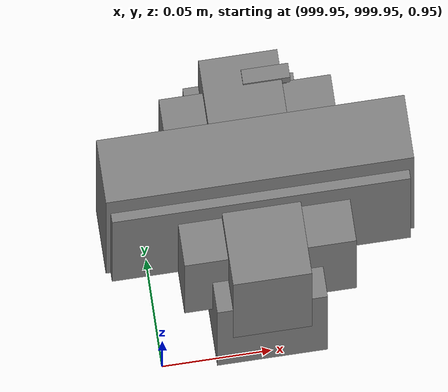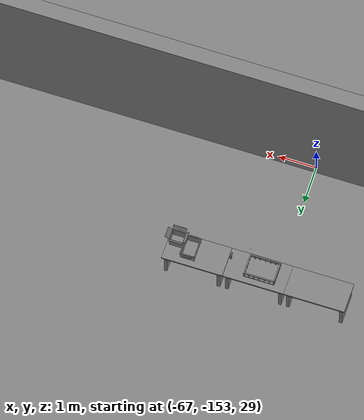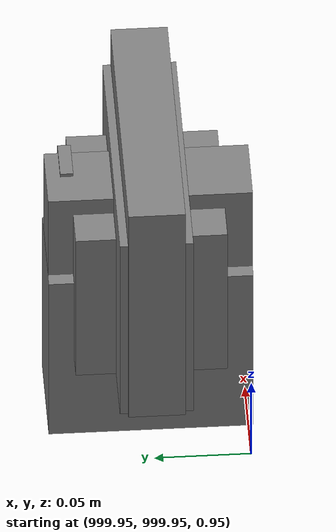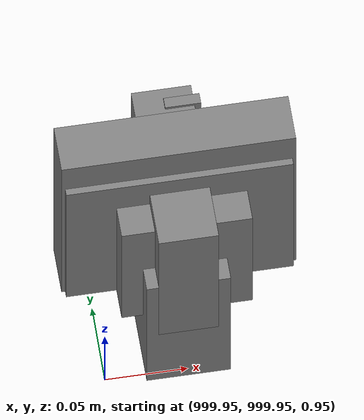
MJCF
<mujoco>
    <option gravity="0.000000000 0.000000000 -9.810000420" timestep="0.0049999999" integrator="implicitfast" density="1.225" viscosity="1.8000001e-05" noslip_iterations="10" iterations="100" sdf_iterations="50">
        <flag multiccd="disable"/>
    </option>
    <size memory="1000M"/>
    <compiler coordinate="local"/>
    <worldbody>
        <light cutoff="30" pos="0 1 1" dir="0 -1 -2"/>
        <light cutoff="30" pos="0 -1 1" dir="0 1 -2"/>
        <body pos="-64.866622925 -149.383972168 30.183746338" euler="89.999984741 89.999946594 0.000000000" name="openloong_gripper_2f85_fix_base_usda_bluebox_01">
            <geom contype="1" conaffinity="1" density="1000" type="box" material="" rgba="0.500000000 0.500000000 0.500000000 1.000000000" solimp="0.899999976 0.949999988 0.001000000" friction="1.000000000 0.005000000 0.000100000" solref="0.020000000 1.000000000" margin="0" condim="3" group="0" pos="0.276580811 0.187225342 0.000068665" quat="0.707106948 0.000077471 0.707106352 0.000077486" size="0.100000001 0.057999998 0.010000000" name="openloong_gripper_2f85_fix_base_usda_geom_F322C0A3_E3E1_49A9_8DF6_4C8F50214BD2"/>
            <geom contype="1" conaffinity="1" density="1000" type="box" material="" rgba="0.500000000 0.500000000 0.500000000 1.000000000" solimp="0.899999976 0.949999988 0.001000000" friction="1.000000000 0.005000000 0.000100000" solref="0.020000000 1.000000000" margin="0" condim="3" group="0" pos="0.000000000 0.002883911 0.000000000" quat="0.999999881 0.000000000 0.000000000 0.000000000" size="0.254000008 0.003000000 0.172000006" name="openloong_gripper_2f85_fix_base_usda_geom_C96876BA_BAC0_4B92_A1A6_BE99B48DDB1D"/>
            <geom contype="1" conaffinity="1" density="1000" type="box" material="" rgba="0.500000000 0.500000000 0.500000000 1.000000000" solimp="0.899999976 0.949999988 0.001000000" friction="1.000000000 0.005000000 0.000100000" solref="0.020000000 1.000000000" margin="0" condim="3" group="0" pos="0.000000000 0.124874115 0.173484802" quat="0.999796331 0.020176515 -0.000000015 0.000000030" size="0.259999990 0.119999997 0.007000000" name="openloong_gripper_2f85_fix_base_usda_geom_B98AD750_0E98_4B3C_9B84_3E14B6A513E7"/>
            <geom contype="1" conaffinity="1" density="1000" type="box" material="" rgba="0.500000000 0.500000000 0.500000000 1.000000000" solimp="0.899999976 0.949999988 0.001000000" friction="1.000000000 0.005000000 0.000100000" solref="0.020000000 1.000000000" margin="0" condim="3" group="0" pos="0.000000000 0.124874115 -0.173469543" quat="0.999796331 -0.020176545 -0.000000015 0.000000000" size="0.259999990 0.119999997 0.007000000" name="openloong_gripper_2f85_fix_base_usda_geom_AD44E4A3_9E9E_472E_96D3_3EC9BC9069F0"/>
            <geom contype="1" conaffinity="1" density="1000" type="box" material="" rgba="0.500000000 0.500000000 0.500000000 1.000000000" solimp="0.899999976 0.949999988 0.001000000" friction="1.000000000 0.005000000 0.000100000" solref="0.020000000 1.000000000" margin="0" condim="3" group="0" pos="0.000000000 0.214008331 0.188980103" quat="0.999912977 0.013176724 0.000000015 0.000000000" size="0.259999990 0.029999999 0.012500000" name="openloong_gripper_2f85_fix_base_usda_geom_D7E26FF6_F6C2_49D8_AFB7_F99B95FA5578"/>
            <geom contype="1" conaffinity="1" density="1000" type="box" material="" rgba="0.500000000 0.500000000 0.500000000 1.000000000" solimp="0.899999976 0.949999988 0.001000000" friction="1.000000000 0.005000000 0.000100000" solref="0.020000000 1.000000000" margin="0" condim="3" group="0" pos="-0.258361816 0.125289917 0.001876831" quat="0.702796936 -0.020792112 0.710783124 0.020769298" size="0.189999998 0.119999997 0.009000000" name="openloong_gripper_2f85_fix_base_usda_geom_49E6B71A_1DE1_478F_9213_24371A8D2491"/>
            <geom contype="1" conaffinity="1" density="1000" type="box" material="" rgba="0.500000000 0.500000000 0.500000000 1.000000000" solimp="0.899999976 0.949999988 0.001000000" friction="1.000000000 0.005000000 0.000100000" solref="0.020000000 1.000000000" margin="0" condim="3" group="0" pos="0.000000000 0.214008331 -0.188980103" quat="0.999912977 -0.013176769 0.000000030 0.000000015" size="0.259999990 0.029999999 0.012500000" name="openloong_gripper_2f85_fix_base_usda_geom_1A9C43AC_4114_4337_8922_5DE546F36706"/>
            <geom contype="1" conaffinity="1" density="1000" type="box" material="" rgba="0.500000000 0.500000000 0.500000000 1.000000000" solimp="0.899999976 0.949999988 0.001000000" friction="1.000000000 0.005000000 0.000100000" solref="0.020000000 1.000000000" margin="0" condim="3" group="0" pos="-0.276611328 0.187225342 0.000068665" quat="0.707106650 0.000077441 0.707106709 0.000077456" size="0.100000001 0.057999998 0.010000000" name="openloong_gripper_2f85_fix_base_usda_geom_2DE989F6_741C_4D89_AD6A_537564C77B08"/>
            <geom contype="1" conaffinity="1" density="1000" type="box" material="" rgba="0.500000000 0.500000000 0.500000000 1.000000000" solimp="0.899999976 0.949999988 0.001000000" friction="1.000000000 0.005000000 0.000100000" solref="0.020000000 1.000000000" margin="0" condim="3" group="0" pos="0.258331299 0.125289917 0.001876831" quat="0.702851415 0.018856421 0.710823774 -0.019329369" size="0.189999998 0.119999997 0.009000000" name="openloong_gripper_2f85_fix_base_usda_geom_63C49C8A_C8A5_46D5_8876_4F24930F77F5"/>
            <freejoint name="openloong_gripper_2f85_fix_base_usda_bluebox_01_joint"/>
            <site size="0.005000000 0.005000000 0.005000000" rgba="0.500000000 0.500000000 0.500000000 1.000000000" pos="0.000000000 0.000000000 0.000000000" quat="0.999961913 0.008726534 0.000000000 0.000000000" group="0" type="sphere" name="openloong_gripper_2f85_fix_base_usda_bluebox_01site"/>
        </body>
        <body pos="-64.496299744 -149.491867065 30.235729218" euler="0.000000000 0.000000000 89.999946594" name="openloong_gripper_2f85_fix_base_usda_cardboardbox_01">
            <geom contype="1" conaffinity="1" density="1000" type="box" material="" rgba="0.500000000 0.500000000 0.500000000 1.000000000" solimp="0.899999976 0.949999988 0.001000000" friction="1.000000000 0.005000000 0.000100000" solref="0.020000000 1.000000000" margin="0" condim="3" group="0" pos="-0.003166199 -0.004086494 0.005052090" quat="1.000000000 0.000000000 0.000000000 0.000000000" size="0.142499998 0.177500010 0.005000000" name="openloong_gripper_2f85_fix_base_usda_geom_C4AEC18B_4FFC_4ED9_8A6A_8CD451E71068"/>
            <geom contype="1" conaffinity="1" density="1000" type="box" material="" rgba="0.500000000 0.500000000 0.500000000 1.000000000" solimp="0.899999976 0.949999988 0.001000000" friction="1.000000000 0.005000000 0.000100000" solref="0.020000000 1.000000000" margin="0" condim="3" group="0" pos="-0.003166199 0.170316696 0.150570869" quat="1.000000000 0.000000000 0.000000000 0.000000000" size="0.142499998 0.005000000 0.149999991" name="openloong_gripper_2f85_fix_base_usda_geom_618074CA_AB35_411A_BCC0_36E996FDDE2D"/>
            <geom contype="1" conaffinity="1" density="1000" type="box" material="" rgba="0.500000000 0.500000000 0.500000000 1.000000000" solimp="0.899999976 0.949999988 0.001000000" friction="1.000000000 0.005000000 0.000100000" solref="0.020000000 1.000000000" margin="0" condim="3" group="0" pos="-0.147399902 -0.005307198 0.150570869" quat="1.000000000 0.000000000 0.000000000 0.000000000" size="0.005000000 0.177500010 0.149999991" name="openloong_gripper_2f85_fix_base_usda_geom_EA2D185D_E331_4C24_84DE_4F00DE242356"/>
            <geom contype="1" conaffinity="1" density="1000" type="box" material="" rgba="0.500000000 0.500000000 0.500000000 1.000000000" solimp="0.899999976 0.949999988 0.001000000" friction="1.000000000 0.005000000 0.000100000" solref="0.020000000 1.000000000" margin="0" condim="3" group="0" pos="0.140275955 -0.005307198 0.150570869" quat="1.000000000 0.000000000 0.000000000 0.000000000" size="0.005000000 0.177500010 0.149999991" name="openloong_gripper_2f85_fix_base_usda_geom_FAE5DC1C_D9C6_4387_9660_075009033BD4"/>
            <geom contype="1" conaffinity="1" density="1000" type="box" material="" rgba="0.500000000 0.500000000 0.500000000 1.000000000" solimp="0.899999976 0.949999988 0.001000000" friction="1.000000000 0.005000000 0.000100000" solref="0.020000000 1.000000000" margin="0" condim="3" group="0" pos="-0.003166199 -0.181550980 0.150570869" quat="1.000000000 0.000000000 0.000000000 0.000000000" size="0.142499998 0.005000000 0.149999991" name="openloong_gripper_2f85_fix_base_usda_geom_B4314786_2AC8_4741_85B8_7EB6DED2CCCE"/>
            <freejoint name="openloong_gripper_2f85_fix_base_usda_cardboardbox_01_joint"/>
            <site size="0.005000000 0.005000000 0.005000000" rgba="0.500000000 0.500000000 0.500000000 1.000000000" pos="0.000000000 0.000000000 0.000000000" quat="0.999961913 0.008726535 0.000000000 0.000000000" group="0" type="sphere" name="openloong_gripper_2f85_fix_base_usda_site_BDE5ACB1_3E58_49D1_B42F_E50AC5373042"/>
            <body pos="0.139160156 -0.004048347 0.301930904" euler="-179.999954224 49.383502960 179.999954224" name="openloong_gripper_2f85_fix_base_usda_A1_006">
                <geom contype="1" conaffinity="1" density="1000" type="box" material="" rgba="0.500000000 0.500000000 0.500000000 1.000000000" solimp="0.899999976 0.949999988 0.001000000" friction="1.000000000 0.005000000 0.000100000" solref="0.020000000 1.000000000" margin="0" condim="3" group="0" pos="-0.071587563 0.000009537 0.001745224" quat="0.999999881 0.000000000 0.000000000 0.000000000" size="0.071249999 0.179999992 0.002500000" name="openloong_gripper_2f85_fix_base_usda_geom_BCAEAAF5_58E8_4A52_94DF_4CBFBB9858F6"/>
                <joint armature="0" stiffness="0.07" damping="0.0099999998" axis="0.000000 1.000000 0.000000" type="hinge" name="openloong_gripper_2f85_fix_base_usda_A1_006"/>
            </body>
            <body pos="-0.145902634 -0.004086494 0.301938057" euler="-180.000000000 -60.000011444 -180.000000000" name="openloong_gripper_2f85_fix_base_usda_A2_006">
                <geom contype="1" conaffinity="1" density="1000" type="box" material="" rgba="0.500000000 0.500000000 0.500000000 1.000000000" solimp="0.899999976 0.949999988 0.001000000" friction="1.000000000 0.005000000 0.000100000" solref="0.020000000 1.000000000" margin="0" condim="3" group="0" pos="0.071268082 0.000009537 0.002717972" quat="0.000002921 0.000000000 -0.000000030 0.999999881" size="0.071249999 0.179999992 0.002500000" name="openloong_gripper_2f85_fix_base_usda_geom_9168C51F_9AFF_476C_902C_E87B49953456"/>
                <joint armature="0" stiffness="0.07" damping="0.0099999998" axis="0.000000 1.000000 0.000000" type="hinge" name="openloong_gripper_2f85_fix_base_usda_A2_006"/>
            </body>
            <body pos="-0.003385544 0.175991058 0.301930904" euler="-125.858116150 -0.000004561 0.000002331" name="openloong_gripper_2f85_fix_base_usda_B2_006">
                <geom contype="1" conaffinity="1" density="1000" type="box" material="" rgba="0.500000000 0.500000000 0.500000000 1.000000000" solimp="0.899999976 0.949999988 0.001000000" friction="1.000000000 0.005000000 0.000100000" solref="0.020000000 1.000000000" margin="0" condim="3" group="0" pos="0.000009537 -0.070939064 -0.002470016" quat="0.999614120 0.027776197 -0.000000015 0.000000030" size="0.137500003 0.064999998 0.005000000" name="openloong_gripper_2f85_fix_base_usda_geom_2B64CC6D_B5D7_4A63_84F1_644A8408781B"/>
                <joint armature="0" stiffness="0.07" damping="0.0099999998" axis="1.000000 0.000000 0.000000" type="hinge" name="openloong_gripper_2f85_fix_base_usda_B2_006"/>
            </body>
            <body pos="-0.003385544 -0.184140205 0.301938057" euler="147.805557251 0.000000000 0.000000000" name="openloong_gripper_2f85_fix_base_usda_B1_006">
                <geom contype="1" conaffinity="1" density="1000" type="box" material="" rgba="0.500000000 0.500000000 0.500000000 1.000000000" solimp="0.899999976 0.949999988 0.001000000" friction="1.000000000 0.005000000 0.000100000" solref="0.020000000 1.000000000" margin="0" condim="3" group="0" pos="-0.000028610 0.070202351 -0.002703667" quat="0.999614179 -0.027776167 0.000000000 0.000000000" size="0.137500003 0.064999998 0.005000000" name="openloong_gripper_2f85_fix_base_usda_geom_356F2483_1EDD_4072_88C6_E4F1ACC6DF9F"/>
                <joint armature="0" stiffness="0.07" damping="0.0099999998" axis="1.000000 0.000000 0.000000" type="hinge" name="openloong_gripper_2f85_fix_base_usda_B1_006"/>
            </body>
        </body>
        <body pos="-65.882858276 -149.481979370 30.229999542" euler="-64.487716675 0.000000000 0.000000000" name="openloong_gripper_2f85_fix_base_usda_Barcode">
            <geom contype="1" conaffinity="1" density="1000" type="box" material="" rgba="0.500000000 0.500000000 0.500000000 1.000000000" solimp="0.899999976 0.949999988 0.001000000" friction="1.000000000 0.005000000 0.000100000" solref="0.020000000 1.000000000" margin="0" condim="3" group="0" pos="0.000000000 0.013038635 0.001419067" quat="0.000000000 0.000000000 0.000000000 1.000000119" size="0.034000002 0.010000000 0.017999999" name="openloong_gripper_2f85_fix_base_usda_geom_3C20D4BE_6DA2_4EB6_9048_674C409E9570"/>
            <geom contype="1" conaffinity="1" density="1000" type="box" material="" rgba="0.500000000 0.500000000 0.500000000 1.000000000" solimp="0.899999976 0.949999988 0.001000000" friction="1.000000000 0.005000000 0.000100000" solref="0.020000000 1.000000000" margin="0" condim="3" group="0" pos="0.000000000 -0.035301208 -0.007095337" quat="0.000000000 0.000000000 -0.043619365 0.999048233" size="0.028999999 0.010000000 0.020000000" name="openloong_gripper_2f85_fix_base_usda_geom_28F461D1_1609_44B9_B0C7_1BA323CF6A80"/>
            <geom contype="1" conaffinity="1" density="1000" type="box" material="" rgba="0.500000000 0.500000000 0.500000000 1.000000000" solimp="0.899999976 0.949999988 0.001000000" friction="1.000000000 0.005000000 0.000100000" solref="0.020000000 1.000000000" margin="0" condim="3" group="0" pos="0.000000000 -0.043411255 -0.011749268" quat="0.922262907 0.386563420 0.000000000 0.000000000" size="0.026000001 0.010000000 0.020000000" name="openloong_gripper_2f85_fix_base_usda_geom_B011B4A7_55D3_4D16_A02A_2C439A1F4CD4"/>
            <geom contype="1" conaffinity="1" density="1000" type="box" material="" rgba="0.500000000 0.500000000 0.500000000 1.000000000" solimp="0.899999976 0.949999988 0.001000000" friction="1.000000000 0.005000000 0.000100000" solref="0.020000000 1.000000000" margin="0" condim="3" group="0" pos="0.000000000 -0.016967773 -0.031860352" quat="0.000000000 0.000000000 0.000000000 1.000000119" size="0.008000000 0.010000000 0.013000000" name="openloong_gripper_2f85_fix_base_usda_geom_AFFD9316_CBCF_490C_A51F_5D8DCA09C60D"/>
            <geom contype="1" conaffinity="1" density="1000" type="box" material="" rgba="0.500000000 0.500000000 0.500000000 1.000000000" solimp="0.899999976 0.949999988 0.001000000" friction="1.000000000 0.005000000 0.000100000" solref="0.020000000 1.000000000" margin="0" condim="3" group="0" pos="0.000000000 -0.001869202 0.000312805" quat="0.953716993 0.300705761 0.000000000 0.000000000" size="0.032000002 0.010000000 0.018999999" name="openloong_gripper_2f85_fix_base_usda_geom_CD1CF2B6_8B92_4207_AB3B_E2A76C437AEB"/>
            <geom contype="1" conaffinity="1" density="1000" type="box" material="" rgba="0.500000000 0.500000000 0.500000000 1.000000000" solimp="0.899999976 0.949999988 0.001000000" friction="1.000000000 0.005000000 0.000100000" solref="0.020000000 1.000000000" margin="0" condim="3" group="0" pos="0.000000000 -0.019531250 -0.003173828" quat="0.953716993 0.300705761 0.000000000 0.000000000" size="0.030999999 0.010000000 0.020000000" name="openloong_gripper_2f85_fix_base_usda_geom_4D6B401E_5C5C_4BD5_A889_85C7CAC59C0D"/>
            <geom contype="1" conaffinity="1" density="1000" type="box" material="" rgba="0.500000000 0.500000000 0.500000000 1.000000000" solimp="0.899999976 0.949999988 0.001000000" friction="1.000000000 0.005000000 0.000100000" solref="0.020000000 1.000000000" margin="0" condim="3" group="0" pos="0.000000000 -0.035301208 -0.007095337" quat="0.953716993 0.300705761 0.000000000 0.000000000" size="0.028999999 0.010000000 0.020000000" name="openloong_gripper_2f85_fix_base_usda_geom_2E08179E_2F67_46DE_B3D8_744C654CE5A7"/>
            <geom contype="1" conaffinity="1" density="1000" type="box" material="" rgba="0.500000000 0.500000000 0.500000000 1.000000000" solimp="0.899999976 0.949999988 0.001000000" friction="1.000000000 0.005000000 0.000100000" solref="0.020000000 1.000000000" margin="0" condim="3" group="0" pos="0.000000000 -0.042617798 -0.071121216" quat="0.000000000 0.000000000 0.000000000 1.000000119" size="0.013000000 0.021000000 0.059999999" name="openloong_gripper_2f85_fix_base_usda_geom_DA60A450_0E69_457D_8D3E_3BC91E73D6CE"/>
            <freejoint name="openloong_gripper_2f85_fix_base_usda_Barcode_joint"/>
            <site size="0.005000000 0.005000000 0.005000000" rgba="0.500000000 0.500000000 0.500000000 1.000000000" pos="0.000000000 0.000000000 0.000000000" quat="1.000000000 0.000000000 0.000000000 0.000000000" group="0" type="sphere" name="openloong_gripper_2f85_fix_base_usda_Barcode_site"/>
        </body>
        <body pos="-66.745018005 -149.392349243 30.184000015" euler="0.000000000 0.000000000 89.999946594" name="[22333280109741]_Basket_01">
            <geom contype="1" conaffinity="1" density="1000" type="box" material="" rgba="0.500000000 0.500000000 0.500000000 1.000000000" solimp="0.899999976 0.949999988 0.001000000" friction="1.000000000 0.005000000 0.000100000" solref="0.020000000 1.000000000" margin="0" condim="3" group="0" pos="-0.052425385 0.389207840 0.089787483" quat="0.707107008 0.000000000 0.000000000 0.707106411" size="0.014249999 0.014249999 0.059999999" name="[22333280109741]_geom_14453C28_DD2A_4884_9CAE_0E0CF57808C7"/>
            <geom contype="1" conaffinity="1" density="1000" type="box" material="" rgba="0.500000000 0.500000000 0.500000000 1.000000000" solimp="0.899999976 0.949999988 0.001000000" friction="1.000000000 0.005000000 0.000100000" solref="0.020000000 1.000000000" margin="0" condim="3" group="0" pos="0.264015198 -0.133043289 0.089787483" quat="0.707107008 0.000000000 0.000000000 0.707106411" size="0.014249999 0.014249999 0.059999999" name="[22333280109741]_geom_60524AC5_5CE7_4678_AC51_69B31461F3E1"/>
            <geom contype="1" conaffinity="1" density="1000" type="box" material="" rgba="0.500000000 0.500000000 0.500000000 1.000000000" solimp="0.899999976 0.949999988 0.001000000" friction="1.000000000 0.005000000 0.000100000" solref="0.020000000 1.000000000" margin="0" condim="3" group="0" pos="-0.264015198 -0.265548706 0.089793205" quat="0.707107008 0.000000000 0.000000000 0.707106411" size="0.014249999 0.014249999 0.059999999" name="[22333280109741]_geom_FF3703F5_2592_479F_A4E7_884964D8E43A"/>
            <geom contype="1" conaffinity="1" density="1000" type="box" material="" rgba="0.500000000 0.500000000 0.500000000 1.000000000" solimp="0.899999976 0.949999988 0.001000000" friction="1.000000000 0.005000000 0.000100000" solref="0.020000000 1.000000000" margin="0" condim="3" group="0" pos="-0.160263062 -0.389322281 0.089793205" quat="0.707107008 0.000000000 0.000000000 0.707106411" size="0.014249999 0.014249999 0.059999999" name="[22333280109741]_geom_40383F70_2ADB_4DFB_B261_E36BEF19BEA6"/>
            <geom contype="1" conaffinity="1" density="1000" type="box" material="" rgba="0.500000000 0.500000000 0.500000000 1.000000000" solimp="0.899999976 0.949999988 0.001000000" friction="1.000000000 0.005000000 0.000100000" solref="0.020000000 1.000000000" margin="0" condim="3" group="0" pos="0.162265778 -0.389322281 0.089787483" quat="0.707107008 0.000000000 0.000000000 0.707106411" size="0.014249999 0.014249999 0.059999999" name="[22333280109741]_geom_6859902C_3E61_4FD2_B6DA_066052990B12"/>
            <geom contype="1" conaffinity="1" density="1000" type="box" material="" rgba="0.500000000 0.500000000 0.500000000 1.000000000" solimp="0.899999976 0.949999988 0.001000000" friction="1.000000000 0.005000000 0.000100000" solref="0.020000000 1.000000000" margin="0" condim="3" group="0" pos="0.264015198 0.389207840 0.089787483" quat="0.707107008 0.000000000 0.000000000 0.707106411" size="0.014249999 0.014249999 0.059999999" name="[22333280109741]_geom_F7EA998B_AEB3_4B21_B4A7_73E53CB656B5"/>
            <geom contype="1" conaffinity="1" density="1000" type="box" material="" rgba="0.500000000 0.500000000 0.500000000 1.000000000" solimp="0.899999976 0.949999988 0.001000000" friction="1.000000000 0.005000000 0.000100000" solref="0.020000000 1.000000000" margin="0" condim="3" group="0" pos="-0.264015198 -0.133043289 0.089793205" quat="0.707107008 0.000000000 0.000000000 0.707106411" size="0.014249999 0.014249999 0.059999999" name="[22333280109741]_geom_CD9BD499_B528_455E_8245_B39A40A92642"/>
            <geom contype="1" conaffinity="1" density="1000" type="box" material="" rgba="0.500000000 0.500000000 0.500000000 1.000000000" solimp="0.899999976 0.949999988 0.001000000" friction="1.000000000 0.005000000 0.000100000" solref="0.020000000 1.000000000" margin="0" condim="3" group="0" pos="-0.264026642 0.269256592 0.089793205" quat="0.707107008 0.000000000 0.000000000 0.707106411" size="0.014249999 0.014249999 0.059999999" name="[22333280109741]_geom_2C4F938A_B855_4696_A886_39170314FADF"/>
            <geom contype="1" conaffinity="1" density="1000" type="box" material="" rgba="0.500000000 0.500000000 0.500000000 1.000000000" solimp="0.899999976 0.949999988 0.001000000" friction="1.000000000 0.005000000 0.000100000" solref="0.020000000 1.000000000" margin="0" condim="3" group="0" pos="0.054462433 0.389207840 0.089787483" quat="0.707107008 0.000000000 0.000000000 0.707106411" size="0.014249999 0.014249999 0.059999999" name="[22333280109741]_geom_D9AC2D43_F546_4059_8DDA_B13D69193B32"/>
            <geom contype="1" conaffinity="1" density="1000" type="box" material="" rgba="0.500000000 0.500000000 0.500000000 1.000000000" solimp="0.899999976 0.949999988 0.001000000" friction="1.000000000 0.005000000 0.000100000" solref="0.020000000 1.000000000" margin="0" condim="3" group="0" pos="0.054462433 -0.389322281 0.089787483" quat="0.707107008 0.000000000 0.000000000 0.707106411" size="0.014249999 0.014249999 0.059999999" name="[22333280109741]_geom_D7F1AFB6_E3DB_4E1E_BA00_B59B16B1DC08"/>
            <geom contype="1" conaffinity="1" density="1000" type="box" material="" rgba="0.500000000 0.500000000 0.500000000 1.000000000" solimp="0.899999976 0.949999988 0.001000000" friction="1.000000000 0.005000000 0.000100000" solref="0.020000000 1.000000000" margin="0" condim="3" group="0" pos="0.264015198 0.269256592 0.089793205" quat="0.707107008 0.000000000 0.000000000 0.707106411" size="0.014249999 0.014249999 0.059999999" name="[22333280109741]_geom_8D8448E6_FE79_4287_920A_40420FBD6BD2"/>
            <geom contype="1" conaffinity="1" density="1000" type="box" material="" rgba="0.500000000 0.500000000 0.500000000 1.000000000" solimp="0.899999976 0.949999988 0.001000000" friction="1.000000000 0.005000000 0.000100000" solref="0.020000000 1.000000000" margin="0" condim="3" group="0" pos="0.264015198 -0.389322281 0.089787483" quat="0.707107008 0.000000000 0.000000000 0.707106411" size="0.014249999 0.014249999 0.059999999" name="[22333280109741]_geom_0AE1B5FD_1A3B_470F_BBE5_2659C4A274EA"/>
            <geom contype="1" conaffinity="1" density="1000" type="box" material="" rgba="0.500000000 0.500000000 0.500000000 1.000000000" solimp="0.899999976 0.949999988 0.001000000" friction="1.000000000 0.005000000 0.000100000" solref="0.020000000 1.000000000" margin="0" condim="3" group="0" pos="0.000000000 0.000000000 0.015998840" quat="0.707107008 0.000000000 0.000000000 0.707106411" size="0.403499991 0.279000014 0.015750000" name="[22333280109741]_geom_2AC5C2B5_8076_46F5_862D_040241CB1497"/>
            <geom contype="1" conaffinity="1" density="1000" type="box" material="" rgba="0.500000000 0.500000000 0.500000000 1.000000000" solimp="0.899999976 0.949999988 0.001000000" friction="1.000000000 0.005000000 0.000100000" solref="0.020000000 1.000000000" margin="0" condim="3" group="0" pos="0.000000000 -0.389476776 0.163619041" quat="0.707107008 0.000000000 0.000000000 0.707106411" size="0.015000000 0.277500004 0.015750000" name="[22333280109741]_geom_57F0648B_DC1C_4DC1_A7C3_789752F33676"/>
            <geom contype="1" conaffinity="1" density="1000" type="box" material="" rgba="0.500000000 0.500000000 0.500000000 1.000000000" solimp="0.899999976 0.949999988 0.001000000" friction="1.000000000 0.005000000 0.000100000" solref="0.020000000 1.000000000" margin="0" condim="3" group="0" pos="0.162265778 0.389207840 0.089787483" quat="0.707107008 0.000000000 0.000000000 0.707106411" size="0.014249999 0.014249999 0.059999999" name="[22333280109741]_geom_0C329E87_9183_4F4C_A667_8DD042A53239"/>
            <geom contype="1" conaffinity="1" density="1000" type="box" material="" rgba="0.500000000 0.500000000 0.500000000 1.000000000" solimp="0.899999976 0.949999988 0.001000000" friction="1.000000000 0.005000000 0.000100000" solref="0.020000000 1.000000000" margin="0" condim="3" group="0" pos="0.000000000 0.389471054 0.163619041" quat="0.707107008 0.000000000 0.000000000 0.707106411" size="0.015000000 0.277500004 0.015750000" name="[22333280109741]_geom_915284BA_3ED6_4C99_92AD_A77CDB49F542"/>
            <geom contype="1" conaffinity="1" density="1000" type="box" material="" rgba="0.500000000 0.500000000 0.500000000 1.000000000" solimp="0.899999976 0.949999988 0.001000000" friction="1.000000000 0.005000000 0.000100000" solref="0.020000000 1.000000000" margin="0" condim="3" group="0" pos="-0.263511658 0.000000000 0.163619041" quat="0.707107008 0.000000000 0.000000000 0.707106411" size="0.403499991 0.015000000 0.015750000" name="[22333280109741]_geom_7084602A_3DF3_4730_968B_4729B3C7F20E"/>
            <geom contype="1" conaffinity="1" density="1000" type="box" material="" rgba="0.500000000 0.500000000 0.500000000 1.000000000" solimp="0.899999976 0.949999988 0.001000000" friction="1.000000000 0.005000000 0.000100000" solref="0.020000000 1.000000000" margin="0" condim="3" group="0" pos="-0.264015198 0.141334534 0.089793205" quat="0.707107008 0.000000000 0.000000000 0.707106411" size="0.014249999 0.014249999 0.059999999" name="[22333280109741]_geom_BFE188BE_B373_47B9_906B_A67023F05C94"/>
            <geom contype="1" conaffinity="1" density="1000" type="box" material="" rgba="0.500000000 0.500000000 0.500000000 1.000000000" solimp="0.899999976 0.949999988 0.001000000" friction="1.000000000 0.005000000 0.000100000" solref="0.020000000 1.000000000" margin="0" condim="3" group="0" pos="0.264015198 -0.265548706 0.089787483" quat="0.707107008 0.000000000 0.000000000 0.707106411" size="0.014249999 0.014249999 0.059999999" name="[22333280109741]_geom_012E2739_FA15_4512_B841_9CC0112BEBE4"/>
            <geom contype="1" conaffinity="1" density="1000" type="box" material="" rgba="0.500000000 0.500000000 0.500000000 1.000000000" solimp="0.899999976 0.949999988 0.001000000" friction="1.000000000 0.005000000 0.000100000" solref="0.020000000 1.000000000" margin="0" condim="3" group="0" pos="-0.160263062 0.389207840 0.089787483" quat="0.707107008 0.000000000 0.000000000 0.707106411" size="0.014249999 0.014249999 0.059999999" name="[22333280109741]_geom_36C18369_B29E_42DA_95B3_8FD4CFCF311F"/>
            <geom contype="1" conaffinity="1" density="1000" type="box" material="" rgba="0.500000000 0.500000000 0.500000000 1.000000000" solimp="0.899999976 0.949999988 0.001000000" friction="1.000000000 0.005000000 0.000100000" solref="0.020000000 1.000000000" margin="0" condim="3" group="0" pos="-0.052425385 -0.389322281 0.089787483" quat="0.707107008 0.000000000 0.000000000 0.707106411" size="0.014249999 0.014249999 0.059999999" name="[22333280109741]_geom_975E06CB_0129_4AC7_A6F1_C652BDEB342B"/>
            <geom contype="1" conaffinity="1" density="1000" type="box" material="" rgba="0.500000000 0.500000000 0.500000000 1.000000000" solimp="0.899999976 0.949999988 0.001000000" friction="1.000000000 0.005000000 0.000100000" solref="0.020000000 1.000000000" margin="0" condim="3" group="0" pos="-0.264026642 -0.389322281 0.089793205" quat="0.707107008 0.000000000 0.000000000 0.707106411" size="0.014249999 0.014249999 0.059999999" name="[22333280109741]_geom_217D641D_79D4_4336_8B72_7257806C3D01"/>
            <geom contype="1" conaffinity="1" density="1000" type="box" material="" rgba="0.500000000 0.500000000 0.500000000 1.000000000" solimp="0.899999976 0.949999988 0.001000000" friction="1.000000000 0.005000000 0.000100000" solref="0.020000000 1.000000000" margin="0" condim="3" group="0" pos="0.264015198 0.141334534 0.089787483" quat="0.707107008 0.000000000 0.000000000 0.707106411" size="0.014249999 0.014249999 0.059999999" name="[22333280109741]_geom_6C3F3C0F_64DA_4034_955F_F154BB9C1C10"/>
            <geom contype="1" conaffinity="1" density="1000" type="box" material="" rgba="0.500000000 0.500000000 0.500000000 1.000000000" solimp="0.899999976 0.949999988 0.001000000" friction="1.000000000 0.005000000 0.000100000" solref="0.020000000 1.000000000" margin="0" condim="3" group="0" pos="-0.264015198 0.389207840 0.089793205" quat="0.707107008 0.000000000 0.000000000 0.707106411" size="0.014249999 0.014249999 0.059999999" name="[22333280109741]_geom_BF2074DC_B14C_46B2_B108_B4C831051402"/>
            <geom contype="1" conaffinity="1" density="1000" type="box" material="" rgba="0.500000000 0.500000000 0.500000000 1.000000000" solimp="0.899999976 0.949999988 0.001000000" friction="1.000000000 0.005000000 0.000100000" solref="0.020000000 1.000000000" margin="0" condim="3" group="0" pos="0.264015198 0.004480362 0.089787483" quat="0.707107008 0.000000000 0.000000000 0.707106411" size="0.014249999 0.014249999 0.059999999" name="[22333280109741]_geom_00EDE6BB_CD6E_4F12_930A_6C7959DF0E51"/>
            <geom contype="1" conaffinity="1" density="1000" type="box" material="" rgba="0.500000000 0.500000000 0.500000000 1.000000000" solimp="0.899999976 0.949999988 0.001000000" friction="1.000000000 0.005000000 0.000100000" solref="0.020000000 1.000000000" margin="0" condim="3" group="0" pos="0.263694763 -0.000011444 0.163619041" quat="0.707107008 0.000000000 0.000000000 0.707106411" size="0.403499991 0.015000000 0.015750000" name="[22333280109741]_geom_F61EE2F2_12FA_4AEB_ACCE_0E5D98FA9B17"/>
            <geom contype="1" conaffinity="1" density="1000" type="box" material="" rgba="0.500000000 0.500000000 0.500000000 1.000000000" solimp="0.899999976 0.949999988 0.001000000" friction="1.000000000 0.005000000 0.000100000" solref="0.020000000 1.000000000" margin="0" condim="3" group="0" pos="-0.264015198 0.004480362 0.089793205" quat="0.707107008 0.000000000 0.000000000 0.707106411" size="0.014249999 0.014249999 0.059999999" name="[22333280109741]_geom_D0894C8C_5AAB_4732_BBE3_D60BCE03940A"/>
            <freejoint name="[22333280109741]_joint_055263A8_5EEA_4E88_AF94_D8C6601CE24C"/>
        </body>
        <body pos="0.000000000 0.000000000 0.000000000" euler="0.000000000 0.000000000 0.000000000" name="Static Objects_Static Objects">
            <geom contype="1" conaffinity="1" density="1000" type="box" material="" rgba="0.500000000 0.500000000 0.500000000 1.000000000" solimp="0.899999976 0.949999988 0.001000000" friction="1.000000000 0.005000000 0.000100000" solref="0.020000000 1.000000000" margin="0" condim="3" group="0" pos="-67.544113159 -149.365814209 29.727830887" quat="0.500000417 0.499999970 0.499999553 0.499999970" size="0.381000012 0.319999993 0.041000001" name="Static Objects_geom_F5A7C81B_92C1_4965_95A8_40662F825D7C"/>
            <geom contype="1" conaffinity="1" density="1000" type="box" material="" rgba="0.500000000 0.500000000 0.500000000 1.000000000" solimp="0.899999976 0.949999988 0.001000000" friction="1.000000000 0.005000000 0.000100000" solref="0.020000000 1.000000000" margin="0" condim="3" group="0" pos="-68.239501953 -149.365814209 30.086868286" quat="0.500000417 0.499999970 0.499999553 0.499999970" size="0.370999992 0.039500002 0.745000005" name="Static Objects_geom_D41EDE18_3D8E_465A_9401_78E8367250F1"/>
            <geom contype="1" conaffinity="1" density="1000" type="box" material="" rgba="0.500000000 0.500000000 0.500000000 1.000000000" solimp="0.899999976 0.949999988 0.001000000" friction="1.000000000 0.005000000 0.000100000" solref="0.020000000 1.000000000" margin="0" condim="3" group="0" pos="-68.239501953 -149.365814209 30.147235870" quat="0.500000417 0.499999970 0.499999553 0.499999970" size="0.400000006 0.022000000 0.800000012" name="Static Objects_geom_F8EC7477_9BB4_4F6D_8128_AA045D9922FB"/>
            <geom contype="1" conaffinity="1" density="1000" type="box" material="" rgba="0.500000000 0.500000000 0.500000000 1.000000000" solimp="0.899999976 0.949999988 0.001000000" friction="1.000000000 0.005000000 0.000100000" solref="0.020000000 1.000000000" margin="0" condim="3" group="0" pos="-68.934890747 -149.365814209 29.727830887" quat="0.500000417 0.499999970 0.499999553 0.499999970" size="0.381000012 0.319999993 0.041000001" name="Static Objects_geom_45E9855E_7230_4F33_9C91_05A098B11D34"/>
            <geom contype="1" conaffinity="1" density="1000" type="box" material="" rgba="0.500000000 0.500000000 0.500000000 1.000000000" solimp="0.899999976 0.949999988 0.001000000" friction="1.000000000 0.005000000 0.000100000" solref="0.020000000 1.000000000" margin="0" condim="3" group="0" pos="-68.239501953 -149.365814209 29.561563492" quat="0.500000417 0.499999970 0.499999553 0.499999970" size="0.020000000 0.022000000 0.660000026" name="Static Objects_geom_6F74E94D_0560_4079_A524_0B64BFEB1780"/>
            <geom contype="1" conaffinity="1" density="1000" type="box" material="" rgba="0.500000000 0.500000000 0.500000000 1.000000000" solimp="0.899999976 0.949999988 0.001000000" friction="1.000000000 0.005000000 0.000100000" solref="0.020000000 1.000000000" margin="0" condim="3" group="0" pos="-65.945671082 -149.365814209 29.727830887" quat="0.500000417 0.499999970 0.499999553 0.499999970" size="0.381000012 0.319999993 0.041000001" name="Static Objects_geom_8789FCEA_DADC_4B83_A0E8_9DDBCC655ED2"/>
            <geom contype="1" conaffinity="1" density="1000" type="box" material="" rgba="0.500000000 0.500000000 0.500000000 1.000000000" solimp="0.899999976 0.949999988 0.001000000" friction="1.000000000 0.005000000 0.000100000" solref="0.020000000 1.000000000" margin="0" condim="3" group="0" pos="-66.641059875 -149.365814209 30.086868286" quat="0.500000417 0.499999970 0.499999553 0.499999970" size="0.370999992 0.039500002 0.745000005" name="Static Objects_geom_D99A8C64_B45C_46C7_B267_18DE62937E22"/>
            <geom contype="1" conaffinity="1" density="1000" type="box" material="" rgba="0.500000000 0.500000000 0.500000000 1.000000000" solimp="0.899999976 0.949999988 0.001000000" friction="1.000000000 0.005000000 0.000100000" solref="0.020000000 1.000000000" margin="0" condim="3" group="0" pos="-66.641059875 -149.365814209 30.147235870" quat="0.500000417 0.499999970 0.499999553 0.499999970" size="0.400000006 0.022000000 0.800000012" name="Static Objects_geom_CDA6D220_210F_4723_A218_AA5240C3C234"/>
            <geom contype="1" conaffinity="1" density="1000" type="box" material="" rgba="0.500000000 0.500000000 0.500000000 1.000000000" solimp="0.899999976 0.949999988 0.001000000" friction="1.000000000 0.005000000 0.000100000" solref="0.020000000 1.000000000" margin="0" condim="3" group="0" pos="-67.336448669 -149.365814209 29.727830887" quat="0.500000417 0.499999970 0.499999553 0.499999970" size="0.381000012 0.319999993 0.041000001" name="Static Objects_geom_0C0A407A_B683_4880_9B88_116A059917AA"/>
            <geom contype="1" conaffinity="1" density="1000" type="box" material="" rgba="0.500000000 0.500000000 0.500000000 1.000000000" solimp="0.899999976 0.949999988 0.001000000" friction="1.000000000 0.005000000 0.000100000" solref="0.020000000 1.000000000" margin="0" condim="3" group="0" pos="-66.641059875 -149.365814209 29.561563492" quat="0.500000417 0.499999970 0.499999553 0.499999970" size="0.020000000 0.022000000 0.660000026" name="Static Objects_geom_A3148FE0_1914_4D94_BCF6_89B23D4D865E"/>
            <geom contype="1" conaffinity="1" density="1000" type="box" material="" rgba="0.500000000 0.500000000 0.500000000 1.000000000" solimp="0.899999976 0.949999988 0.001000000" friction="1.000000000 0.005000000 0.000100000" solref="0.020000000 1.000000000" margin="0" condim="3" group="0" pos="-64.338577271 -149.365814209 29.727830887" quat="0.500000417 0.499999970 0.499999553 0.499999970" size="0.381000012 0.319999993 0.041000001" name="Static Objects_geom_F9041960_57EB_4BB5_B392_84E8F96577D6"/>
            <geom contype="1" conaffinity="1" density="1000" type="box" material="" rgba="0.500000000 0.500000000 0.500000000 1.000000000" solimp="0.899999976 0.949999988 0.001000000" friction="1.000000000 0.005000000 0.000100000" solref="0.020000000 1.000000000" margin="0" condim="3" group="0" pos="-65.033966064 -149.365814209 30.086868286" quat="0.500000417 0.499999970 0.499999553 0.499999970" size="0.370999992 0.039500002 0.745000005" name="Static Objects_geom_774D11CB_6F1B_4F32_B3D4_BDF832E31650"/>
            <geom contype="1" conaffinity="1" density="1000" type="box" material="" rgba="0.500000000 0.500000000 0.500000000 1.000000000" solimp="0.899999976 0.949999988 0.001000000" friction="1.000000000 0.005000000 0.000100000" solref="0.020000000 1.000000000" margin="0" condim="3" group="0" pos="-65.033966064 -149.365814209 30.147235870" quat="0.500000417 0.499999970 0.499999553 0.499999970" size="0.400000006 0.022000000 0.800000012" name="Static Objects_geom_6A30FC79_33F8_4122_937E_22D1D5790D4C"/>
            <geom contype="1" conaffinity="1" density="1000" type="box" material="" rgba="0.500000000 0.500000000 0.500000000 1.000000000" solimp="0.899999976 0.949999988 0.001000000" friction="1.000000000 0.005000000 0.000100000" solref="0.020000000 1.000000000" margin="0" condim="3" group="0" pos="-65.729354858 -149.365814209 29.727830887" quat="0.500000417 0.499999970 0.499999553 0.499999970" size="0.381000012 0.319999993 0.041000001" name="Static Objects_geom_5A852345_5D2D_4FDD_84FE_54A17AD1ADB1"/>
            <geom contype="1" conaffinity="1" density="1000" type="box" material="" rgba="0.500000000 0.500000000 0.500000000 1.000000000" solimp="0.899999976 0.949999988 0.001000000" friction="1.000000000 0.005000000 0.000100000" solref="0.020000000 1.000000000" margin="0" condim="3" group="0" pos="-65.033966064 -149.365814209 29.561563492" quat="0.500000417 0.499999970 0.499999553 0.499999970" size="0.020000000 0.022000000 0.660000026" name="Static Objects_geom_747F0C98_0642_4BEF_9FF5_F13AC71BD8F2"/>
            <geom contype="1" conaffinity="1" density="1000" type="box" material="" rgba="0.500000000 0.500000000 0.500000000 1.000000000" solimp="0.899999976 0.949999988 0.001000000" friction="1.000000000 0.005000000 0.000100000" solref="0.020000000 1.000000000" margin="0" condim="3" group="0" pos="-61.754566193 -137.853729248 33.906845093" quat="0.707107067 0.000000000 0.000000000 0.707106471" size="0.759999990 0.759999990 4.500000000" name="Static Objects_geom_8684AF66_0E31_4696_8FB4_4DFF0C9C24BC"/>
            <geom contype="1" conaffinity="1" density="1000" type="box" material="" rgba="0.500000000 0.500000000 0.500000000 1.000000000" solimp="0.899999976 0.949999988 0.001000000" friction="1.000000000 0.005000000 0.000100000" solref="0.020000000 1.000000000" margin="0" condim="3" group="0" pos="-57.511135101 -144.927108765 31.707921982" quat="1.000000000 0.000000000 0.000000000 0.000000000" size="0.200000003 8.000000000 2.299999952" name="Static Objects_geom_A7862551_48A2_4AF3_B2E0_AB77AE2E1AA3"/>
            <geom contype="1" conaffinity="1" density="1000" type="box" material="" rgba="0.500000000 0.500000000 0.500000000 1.000000000" solimp="0.899999976 0.949999988 0.001000000" friction="1.000000000 0.005000000 0.000100000" solref="0.020000000 1.000000000" margin="0" condim="3" group="0" pos="-80.517646790 -157.574050903 31.688196182" quat="0.707107067 0.000000000 0.000000000 0.707106471" size="0.600000024 0.600000024 2.299999952" name="Static Objects_geom_52FAC2DD_983B_4636_A6AD_8A9FCA08697A"/>
            <geom contype="1" conaffinity="1" density="1000" type="box" material="" rgba="0.500000000 0.500000000 0.500000000 1.000000000" solimp="0.899999976 0.949999988 0.001000000" friction="1.000000000 0.005000000 0.000100000" solref="0.020000000 1.000000000" margin="0" condim="3" group="0" pos="-80.711044312 -147.414932251 31.666158676" quat="1.000000000 0.000000000 0.000000000 0.000000000" size="0.200000003 10.000000000 2.299999952" name="Static Objects_geom_A97C9483_7BFE_4FE1_8DF2_9F90F3D5FA65"/>
            <geom contype="1" conaffinity="1" density="1000" type="box" material="" rgba="0.500000000 0.500000000 0.500000000 1.000000000" solimp="0.899999976 0.949999988 0.001000000" friction="1.000000000 0.005000000 0.000100000" solref="0.020000000 1.000000000" margin="0" condim="3" group="0" pos="-57.687217712 -137.434692383 31.688196182" quat="0.707107067 0.000000000 0.000000000 0.707106471" size="0.600000024 0.600000024 2.299999952" name="Static Objects_geom_DF55ACB8_EAF3_4136_A61E_66774B565F1B"/>
            <geom contype="1" conaffinity="1" density="1000" type="box" material="" rgba="0.500000000 0.500000000 0.500000000 1.000000000" solimp="0.899999976 0.949999988 0.001000000" friction="1.000000000 0.005000000 0.000100000" solref="0.020000000 1.000000000" margin="0" condim="3" group="0" pos="-69.537033081 -140.263229370 31.714921951" quat="0.707107067 0.000000000 0.000000000 0.707106471" size="0.759999990 4.500000000 2.299999952" name="Static Objects_geom_B0B30C58_5298_4656_A02A_EC2A29FF1399"/>
            <geom contype="1" conaffinity="1" density="1000" type="box" material="" rgba="0.500000000 0.500000000 0.500000000 1.000000000" solimp="0.899999976 0.949999988 0.001000000" friction="1.000000000 0.005000000 0.000100000" solref="0.020000000 1.000000000" margin="0" condim="3" group="0" pos="-80.073638916 -137.853713989 33.906845093" quat="0.707107067 0.000000000 0.000000000 0.707106471" size="0.759999990 0.759999990 4.500000000" name="Static Objects_geom_036B93E0_6EBC_4EEE_ACB1_1C5E9C985FA5"/>
            <geom contype="1" conaffinity="1" density="1000" type="box" material="" rgba="0.500000000 0.500000000 0.500000000 1.000000000" solimp="0.899999976 0.949999988 0.001000000" friction="1.000000000 0.005000000 0.000100000" solref="0.020000000 1.000000000" margin="0" condim="3" group="0" pos="-73.406707764 -155.734664917 31.707921982" quat="1.000000000 0.000000000 0.000000000 0.000000000" size="0.200000003 3.000000000 2.299999952" name="Static Objects_geom_E3969C0A_A7CE_445F_8CA7_B686FE0A8485"/>
            <geom contype="1" conaffinity="1" density="1000" type="box" material="" rgba="0.500000000 0.500000000 0.500000000 1.000000000" solimp="0.899999976 0.949999988 0.001000000" friction="1.000000000 0.005000000 0.000100000" solref="0.020000000 1.000000000" margin="0" condim="3" group="0" pos="-68.497543335 -137.448257446 31.707921982" quat="0.707107067 0.000000000 0.000000000 0.707106471" size="0.200000003 14.000000000 2.299999952" name="Static Objects_geom_560AE730_B36F_49B4_A716_BEB7B3AD6AEE"/>
            <geom contype="1" conaffinity="1" density="1000" type="cylinder" material="" rgba="0.500000000 0.500000000 0.500000000 1.000000000" solimp="0.899999976 0.949999988 0.001000000" friction="1.000000000 0.005000000 0.000100000" solref="0.020000000 1.000000000" margin="0" condim="3" group="0" pos="-68.868522644 -142.134506226 31.711090088" quat="0.707107067 0.000000000 0.000000000 0.707106471" size="0.509999990 2.299999952 1.000000000" name="Static Objects_geom_9A4AD5AB_6C48_443A_818C_83AB7126698D"/>
            <geom contype="1" conaffinity="1" density="1000" type="plane" material="" rgba="0.500000000 0.500000000 0.500000000 1.000000000" solimp="0.899999976 0.949999988 0.001000000" friction="1.000000000 0.005000000 0.000100000" solref="0.020000000 1.000000000" margin="0" condim="3" group="0" pos="-72.873703003 -147.131927490 29.409669876" quat="1.000000000 0.000000000 0.000000000 0.000000000" size="18.000000000 14.000000000 1.000000000" name="Static Objects_geom_8AF12117_7EDB_483A_B480_0DC7A1F20E66"/>
            <geom contype="1" conaffinity="1" density="1000" type="box" material="" rgba="0.500000000 0.500000000 0.500000000 1.000000000" solimp="0.899999976 0.949999988 0.001000000" friction="1.000000000 0.005000000 0.000100000" solref="0.020000000 1.000000000" margin="0" condim="3" group="0" pos="-79.943580627 -157.782272339 31.707921982" quat="0.707107067 0.000000000 0.000000000 0.707106471" size="0.200000003 7.000000000 2.299999952" name="Static Objects_geom_481D8C35_12CA_48F5_891D_C23649470B0E"/>
            <geom contype="1" conaffinity="1" density="1000" type="box" material="" rgba="0.500000000 0.500000000 0.500000000 1.000000000" solimp="0.899999976 0.949999988 0.001000000" friction="1.000000000 0.005000000 0.000100000" solref="0.020000000 1.000000000" margin="0" condim="3" group="0" pos="-65.421028137 -152.903442383 31.707921982" quat="0.707107067 0.000000000 0.000000000 0.707106471" size="0.200000003 7.800000191 2.299999952" name="Static Objects_geom_FC81E70E_0186_4A63_B1B4_C00920462275"/>
            <geom contype="1" conaffinity="1" density="1000" type="box" material="" rgba="0.500000000 0.500000000 0.500000000 1.000000000" solimp="0.899999976 0.949999988 0.001000000" friction="1.000000000 0.005000000 0.000100000" solref="0.020000000 1.000000000" margin="0" condim="3" group="0" pos="-74.776908875 -149.964416504 31.688196182" quat="1.000000000 0.000000000 0.000000000 0.000000000" size="0.600000024 0.409999996 2.299999952" name="Static Objects_geom_494F3AD1_D777_4EB7_8110_0189FDBA6B4E"/>
            <geom contype="1" conaffinity="1" density="1000" type="cylinder" material="" rgba="0.500000000 0.500000000 0.500000000 1.000000000" solimp="0.899999976 0.949999988 0.001000000" friction="1.000000000 0.005000000 0.000100000" solref="0.020000000 1.000000000" margin="0" condim="3" group="0" pos="-60.161884308 -142.134506226 31.711090088" quat="0.707107067 0.000000000 0.000000000 0.707106471" size="0.509999990 2.299999952 1.000000000" name="Static Objects_geom_FD9588DA_97AB_4AA9_81D7_C122C856E2E0"/>
            <geom contype="1" conaffinity="1" density="1000" type="cylinder" material="" rgba="0.500000000 0.500000000 0.500000000 1.000000000" solimp="0.899999976 0.949999988 0.001000000" friction="1.000000000 0.005000000 0.000100000" solref="0.020000000 1.000000000" margin="0" condim="3" group="0" pos="-75.382453918 -149.963455200 31.711090088" quat="0.707107067 0.000000000 0.000000000 0.707106471" size="0.409999996 2.299999952 1.000000000" name="Static Objects_geom_F95F016E_62AF_4C61_A5FF_A6640C74C2BD"/>
            <geom contype="1" conaffinity="1" density="1000" type="cylinder" material="" rgba="0.500000000 0.500000000 0.500000000 1.000000000" solimp="0.899999976 0.949999988 0.001000000" friction="1.000000000 0.005000000 0.000100000" solref="0.020000000 1.000000000" margin="0" condim="3" group="0" pos="-74.154960632 -149.963455200 31.711090088" quat="0.707107067 0.000000000 0.000000000 0.707106471" size="0.409999996 2.299999952 1.000000000" name="Static Objects_geom_20512148_E465_4FD7_A487_BA715F64E375"/>
            <geom contype="1" conaffinity="1" density="1000" type="cylinder" material="" rgba="0.500000000 0.500000000 0.500000000 1.000000000" solimp="0.899999976 0.949999988 0.001000000" friction="1.000000000 0.005000000 0.000100000" solref="0.020000000 1.000000000" margin="0" condim="3" group="0" pos="-77.566612244 -142.134506226 31.711090088" quat="0.707107067 0.000000000 0.000000000 0.707106471" size="0.509999990 2.299999952 1.000000000" name="Static Objects_geom_0EA5D915_BEE1_4F4E_A8C6_4D990A8D8300"/>
        </body>
        <body pos="1000.000000000 1000.000000000 1.000000000" euler="0.000000000 0.000000000 180.000000000" name="openloong_gripper_2f85_fix_base_usda_wifi_box">
            <geom contype="1" conaffinity="1" density="1000" type="box" material="" rgba="0.500000000 0.500000000 0.500000000 1.000000000" solimp="0.899999976 0.949999988 0.001000000" friction="1.000000000 0.005000000 0.000100000" solref="0.020000000 1.000000000" margin="0" condim="3" group="0" pos="0.000000000 0.000000000 0.058978677" quat="0.000000000 0.000000047 0.000000000 1.000000000" size="0.068499997 0.018999999 0.059000000" name="openloong_gripper_2f85_fix_base_usda_geom_BC5B05D6_F3FD_4AAC_94A3_EFE5EA66AEDA"/>
            <freejoint name="openloong_gripper_2f85_fix_base_usda_wifi_box_joint"/>
            <site size="0.005000000 0.005000000 0.005000000" rgba="0.500000000 0.500000000 0.500000000 1.000000000" pos="0.000000000 0.000000000 0.000000000" quat="0.999961913 0.008726500 0.000000000 0.000000000" group="0" type="sphere" name="openloong_gripper_2f85_fix_base_usda_wifi_boxsite"/>
        </body>
        <body pos="-65.903266907 -149.630310059 31.164205551" euler="-56.470466614 29.173553467 115.280647278" mocap="true" name="spotlight2_SpotLight"/>
        <body pos="-65.963188171 -148.991775513 31.162450790" euler="-10.742798805 -68.153915405 67.087142944" mocap="true" name="spotlight1_SpotLight"/>
        <body pos="1000.000000000 999.999938965 1.000000000" euler="0.000000000 0.000000000 180.000000000" name="openloong_gripper_2f85_fix_base_usda_intelcore_i5">
            <geom contype="1" conaffinity="1" density="1000" type="box" material="" rgba="0.500000000 0.500000000 0.500000000 1.000000000" solimp="0.899999976 0.949999988 0.001000000" friction="1.000000000 0.005000000 0.000100000" solref="0.020000000 1.000000000" margin="0" condim="3" group="0" pos="0.000000000 0.000000000 0.051722717" quat="0.707106709 0.000000000 0.000000000 -0.707106769" size="0.052800000 0.018080002 0.052800000" name="openloong_gripper_2f85_fix_base_usda_geom_A3DB30AD_F522_40B1_9B0B_3A4C49EBA3D8"/>
            <freejoint name="openloong_gripper_2f85_fix_base_usda_intelcore_i5_joint"/>
            <site size="0.005000000 0.005000000 0.005000000" rgba="0.500000000 0.500000000 0.500000000 1.000000000" pos="0.000000000 0.000000000 0.000000000" quat="0.999961913 0.008726534 0.000000000 0.000000000" group="0" type="sphere" name="openloong_gripper_2f85_fix_base_usda_intelcore_i5site"/>
        </body>
        <body pos="-66.071136475 -149.277740479 31.165653229" euler="-110.309226990 -8.664969444 -94.247894287" mocap="true" name="spotlight5_SpotLight"/>
        <body pos="1000.000000000 1000.000000000 1.000000000" euler="0.000011953 0.000005123 -179.999984741" name="openloong_gripper_2f85_fix_base_usda_intel_box">
            <geom contype="1" conaffinity="1" density="1000" type="box" material="" rgba="0.500000000 0.500000000 0.500000000 1.000000000" solimp="0.899999976 0.949999988 0.001000000" friction="1.000000000 0.005000000 0.000100000" solref="0.020000000 1.000000000" margin="0" condim="3" group="0" pos="0.000000000 -0.000067139 0.000082284" quat="0.707106709 0.000000225 0.000000253 0.707106650" size="0.052800003 0.025300000 0.052800003" name="openloong_gripper_2f85_fix_base_usda_geom_06576018_EF21_4BDF_A771_48FFFAD76145"/>
            <freejoint name="openloong_gripper_2f85_fix_base_usda_intel_box_joint"/>
            <site size="0.005000000 0.005000000 0.005000000" rgba="0.500000000 0.500000000 0.500000000 1.000000000" pos="0.000000000 0.000000000 0.000000000" quat="0.999961913 0.008726500 0.000000000 0.000000000" group="0" type="sphere" name="openloong_gripper_2f85_fix_base_usda_intel_boxsite"/>
        </body>
        <body pos="1000.000000000 1000.000000000 1.000000000" euler="0.000000000 0.000000000 180.000000000" name="openloong_gripper_2f85_fix_base_usda_cpu_fan">
            <geom contype="1" conaffinity="1" density="1000" type="box" material="" rgba="0.500000000 0.500000000 0.500000000 1.000000000" solimp="0.899999976 0.949999988 0.001000000" friction="1.000000000 0.005000000 0.000100000" solref="0.020000000 1.000000000" margin="0" condim="3" group="0" pos="0.000000000 0.000000000 0.070034981" quat="0.000000000 0.000000000 0.000000000 1.000000000" size="0.070700005 0.014699999 0.070700005" name="openloong_gripper_2f85_fix_base_usda_geom_0C0430B2_6BDE_4B05_8C5C_40314B853127"/>
            <freejoint name="openloong_gripper_2f85_fix_base_usda_cpu_fan_joint"/>
            <site size="0.005000000 0.005000000 0.005000000" rgba="0.500000000 0.500000000 0.500000000 1.000000000" pos="0.000000000 0.000000000 0.000000000" quat="0.999961913 0.008726535 0.000000000 0.000000000" group="0" type="sphere" name="openloong_gripper_2f85_fix_base_usda_cpu_fancsite"/>
        </body>
        <body pos="1000.000000000 1000.000000000 1.000000000" euler="0.000000000 0.000000000 180.000000000" name="openloong_gripper_2f85_fix_base_usda_battery_01">
            <geom contype="1" conaffinity="1" density="1000" type="box" material="" rgba="0.500000000 0.500000000 0.500000000 1.000000000" solimp="0.899999976 0.949999988 0.001000000" friction="1.000000000 0.005000000 0.000100000" solref="0.020000000 1.000000000" margin="0" condim="3" group="0" pos="-0.011123657 -0.041940309 0.101691343" quat="1.000000000 0.000000000 0.000000000 0.000000000" size="0.010800000 0.003375000 0.004725000" name="openloong_gripper_2f85_fix_base_usda_geom_40E93B77_55CE_4171_8E55_AE3982BFA479"/>
            <geom contype="1" conaffinity="1" density="1000" type="box" material="" rgba="0.500000000 0.500000000 0.500000000 1.000000000" solimp="0.899999976 0.949999988 0.001000000" friction="1.000000000 0.005000000 0.000100000" solref="0.020000000 1.000000000" margin="0" condim="3" group="0" pos="-0.010876465 -0.044247437 0.047066893" quat="0.998702705 -0.050920475 0.000000000 0.000000000" size="0.009450001 0.002700000 0.024975000" name="openloong_gripper_2f85_fix_base_usda_geom_636FFB0D_3B3A_4759_91B4_8CABB9343DDE"/>
            <geom contype="1" conaffinity="1" density="1000" type="box" material="" rgba="0.500000000 0.500000000 0.500000000 1.000000000" solimp="0.899999976 0.949999988 0.001000000" friction="1.000000000 0.005000000 0.000100000" solref="0.020000000 1.000000000" margin="0" condim="3" group="0" pos="-0.001235962 -0.000659180 0.047381196" quat="1.000000000 0.000000000 0.000000000 0.000000000" size="0.039420001 0.039150000 0.047250003" name="openloong_gripper_2f85_fix_base_usda_geom_070F8792_5215_4153_949C_371CF5D20B44"/>
            <geom contype="1" conaffinity="1" density="1000" type="box" material="" rgba="0.500000000 0.500000000 0.500000000 1.000000000" solimp="0.899999976 0.949999988 0.001000000" friction="1.000000000 0.005000000 0.000100000" solref="0.020000000 1.000000000" margin="0" condim="3" group="0" pos="-0.010876465 -0.039138794 0.009851727" quat="1.000000000 0.000000000 0.000000000 0.000000000" size="0.009450001 0.010800000 0.013500000" name="openloong_gripper_2f85_fix_base_usda_geom_72CA57EE_3799_41E7_A256_8B375BB86CBF"/>
            <geom contype="1" conaffinity="1" density="1000" type="box" material="" rgba="0.500000000 0.500000000 0.500000000 1.000000000" solimp="0.899999976 0.949999988 0.001000000" friction="1.000000000 0.005000000 0.000100000" solref="0.020000000 1.000000000" margin="0" condim="3" group="0" pos="-0.010876465 -0.041528322 0.071508206" quat="1.000000000 0.000000000 0.000000000 0.000000000" size="0.009450001 0.002700000 0.027000001" name="openloong_gripper_2f85_fix_base_usda_geom_1D7C926F_BCA9_4F17_86B6_F2D27C948D5F"/>
            <freejoint name="openloong_gripper_2f85_fix_base_usda_battery_01_joint"/>
            <site size="0.005000000 0.005000000 0.005000000" rgba="0.500000000 0.500000000 0.500000000 1.000000000" pos="0.000000000 0.000000000 0.000000000" quat="0.999961913 0.008726500 0.000000000 0.000000000" group="0" type="sphere" name="openloong_gripper_2f85_fix_base_usda_battery_01site"/>
        </body>
        <body pos="-66.291030884 -149.869689941 29.018842697" euler="0.000000000 0.000000000 89.999946594" mocap="true" name="openloong_gripper_2f85_fix_base_usda_leftHandMocap"/>
        <body pos="-66.291030884 -149.869689941 29.018842697" euler="0.000000000 0.000000000 89.999946594" mocap="true" name="openloong_gripper_2f85_fix_base_usda_rightHandMocap"/>
        <body pos="-66.291030884 -149.869689941 30.218843460" euler="0.000000000 0.000000000 89.999946594" name="openloong_gripper_2f85_fix_base_usda_base_link">
            <geom contype="1" conaffinity="1" density="1000" type="mesh" material="" rgba="0.783999979 0.783999979 0.783999979 1.000000000" solimp="0.899999976 0.949999988 0.001000000" friction="1.000000000 0.005000000 0.000100000" solref="0.020000000 1.000000000" margin="0" condim="3" group="3" mesh="base_link" pos="0.000000000 0.000000000 0.000000000" quat="1.000000000 0.000000000 0.000000000 0.000000000" size="1.000000000 1.000000000 1.000000000" name="openloong_gripper_2f85_fix_base_usda__geom_7_D52A02A7_4C93_4574_854B_031F7D86B771"/>
            <site size="0.005000000 0.005000000 0.005000000" rgba="0.500000000 0.500000000 0.500000000 1.000000000" pos="0.000000000 0.000000000 0.000000000" quat="1.000000000 0.000000000 0.000000000 0.000000000" group="0" type="sphere" name="openloong_gripper_2f85_fix_base_usda_imu"/>
            <inertial mass="22.447001" pos="-0.005664100 -0.001336700 0.238289997" diaginertia="0.374352545 0.277180195 0.220617250" quat="0.999247074 0.035235517 -0.015086859 0.006023135"/>
            <body pos="0.000000000 0.000000000 0.299997330" euler="0.000000000 0.000000000 0.000000000" name="openloong_gripper_2f85_fix_base_usda_dummy_body">
                <geom contype="1" conaffinity="1" density="1000" type="sphere" material="" rgba="0.783999979 0.783999979 0.783999979 1.000000000" solimp="0.899999976 0.949999988 0.001000000" friction="1.000000000 0.005000000 0.000100000" solref="0.020000000 1.000000000" margin="0" condim="3" group="3" pos="0.000000000 0.000000000 0.000000000" quat="1.000000000 0.000000000 0.000000000 0.000000000" size="0.010000000 0.000000000 0.000000000" name="openloong_gripper_2f85_fix_base_usda__geom_8_90493C4C_DD41_4A80_9D71_8B8312DEF634"/>
                <joint armature="0.0099999998" stiffness="0" damping="0.1" axis="0.000000 0.000000 1.000000" type="hinge" name="openloong_gripper_2f85_fix_base_usda_dummy_joint"/>
                <site size="0.010000000 0.005000000 0.005000000" rgba="0.500000000 0.500000000 0.500000000 1.000000000" pos="0.000000000 0.000000000 0.000000000" quat="1.000000000 0.000000000 0.000000000 0.000000000" group="3" type="sphere" name="openloong_gripper_2f85_fix_base_usda_dummy_site"/>
            </body>
            <body pos="0.009002686 0.000000000 0.406400681" euler="0.000000000 0.000000000 0.000000000" name="openloong_gripper_2f85_fix_base_usda_Link_head_yaw">
                <geom contype="1" conaffinity="1" density="1000" type="mesh" material="" rgba="0.783999979 0.783999979 0.783999979 1.000000000" solimp="0.899999976 0.949999988 0.001000000" friction="1.000000000 0.005000000 0.000100000" solref="0.020000000 1.000000000" margin="0" condim="3" group="3" mesh="Link_head_yaw" pos="0.000000000 0.000000000 0.000000000" quat="1.000000000 0.000000000 0.000000000 0.000000000" size="1.000000000 1.000000000 1.000000000" name="openloong_gripper_2f85_fix_base_usda__geom_10_2F859321_3C0E_43CA_97AD_37119C9447A1"/>
                <inertial mass="0.84249002" pos="0.000000000 -0.002081400 0.044801001" diaginertia="0.000700588 0.000629000 0.000553812" quat="0.706933022 -0.015675601 0.015677100 0.706933022"/>
                <body pos="0.000000000 -0.034599304 0.048500061" euler="0.000000000 0.000000000 0.000000000" name="openloong_gripper_2f85_fix_base_usda_Link_head_pitch">
                    <geom contype="1" conaffinity="1" density="1000" type="mesh" material="" rgba="0.783999979 0.783999979 0.783999979 1.000000000" solimp="0.899999976 0.949999988 0.001000000" friction="1.000000000 0.005000000 0.000100000" solref="0.020000000 1.000000000" margin="0" condim="3" group="3" mesh="Link_head_pitch" pos="0.000000000 0.000000000 0.000000000" quat="1.000000000 0.000000000 0.000000000 0.000000000" size="1.000000000 1.000000000 1.000000000" name="openloong_gripper_2f85_fix_base_usda__geom_12_1A05DA1E_20BD_4A16_9249_2724A6CAA071"/>
                    <inertial mass="1.3943" pos="0.020569000 0.033004001 0.125000000" diaginertia="0.006381400 0.006289940 0.004481460" quat="0.973390222 0.008406822 0.228157058 0.019624906"/>
                    <body pos="0.000000000 0.029998779 0.000000000" euler="0.000000000 0.000000000 0.000000000" name="openloong_gripper_2f85_fix_base_usda_neck_center_body">
                        <site size="0.010000000 0.005000000 0.005000000" rgba="0.500000000 0.500000000 0.500000000 1.000000000" pos="0.000000000 0.000000000 0.000000000" quat="1.000000000 0.000000000 0.000000000 0.000000000" group="3" type="sphere" name="openloong_gripper_2f85_fix_base_usda_neck_center_site"/>
                        <body pos="0.020004272 0.000000000 0.149999619" euler="-0.000002229 39.998176575 -90.000205994" name="openloong_gripper_2f85_fix_base_usda_camera_head">
                            <site size="0.010000000 0.005000000 0.005000000" rgba="0.500000000 0.500000000 0.500000000 1.000000000" pos="0.000000000 0.000000000 0.000000000" quat="1.000000000 0.000000000 0.000000000 0.000000000" group="3" type="sphere" name="openloong_gripper_2f85_fix_base_usda_camera_head_site"/>
                        </body>
                    </body>
                </body>
            </body>
            <body pos="0.003997803 -0.161598206 0.392200470" euler="0.000000000 0.000000000 0.000000000" name="openloong_gripper_2f85_fix_base_usda_Link_arm_r_01">
                <geom contype="1" conaffinity="1" density="1000" type="mesh" material="" rgba="0.783999979 0.783999979 0.783999979 1.000000000" solimp="0.899999976 0.949999988 0.001000000" friction="1.000000000 0.005000000 0.000100000" solref="0.020000000 1.000000000" margin="0" condim="3" group="3" mesh="Link_arm_r_01" pos="0.000000000 0.000000000 0.000000000" quat="1.000000000 0.000000000 0.000000000 0.000000000" size="1.000000000 1.000000000 1.000000000" name="openloong_gripper_2f85_fix_base_usda__geom_14_D9CCAD63_1AF0_4C59_A3A1_321F0DBA40FC"/>
                <joint armature="0.0099999998" stiffness="0" damping="1" axis="0.000000 -1.000000 0.000000" limited="true" range="-170.000015259 170.000015259" type="hinge" name="openloong_gripper_2f85_fix_base_usda_J_arm_r_01"/>
                <inertial mass="0.75641" pos="0.004494600 -0.038293999 -0.000001874" diaginertia="0.000842990 0.000803050 0.000587120" quat="-0.000163502 0.707098067 0.000812463 0.707115054"/>
                <body pos="-0.041992188 -0.041000366 0.000000000" euler="0.000000000 0.000000000 0.000000000" name="openloong_gripper_2f85_fix_base_usda_Link_arm_r_02">
                    <geom contype="1" conaffinity="1" density="1000" type="mesh" material="" rgba="0.783999979 0.783999979 0.783999979 1.000000000" solimp="0.899999976 0.949999988 0.001000000" friction="1.000000000 0.005000000 0.000100000" solref="0.020000000 1.000000000" margin="0" condim="3" group="3" mesh="Link_arm_r_02" pos="0.000000000 0.000000000 0.000000000" quat="1.000000000 0.000000000 0.000000000 0.000000000" size="1.000000000 1.000000000 1.000000000" name="openloong_gripper_2f85_fix_base_usda__geom_16_1BB1FFFF_1667_4E25_884E_DDE537C4FA9C"/>
                    <joint armature="0.0099999998" stiffness="0" damping="1" axis="-1.000000 0.000000 0.000000" limited="true" range="-105.000244141 105.000244141" type="hinge" name="openloong_gripper_2f85_fix_base_usda_J_arm_r_02"/>
                    <inertial mass="0.98500001" pos="0.041999999 -0.067430697 0.000000000" diaginertia="0.002262690 0.001730990 0.001154020" quat="0.500000000 0.500000000 -0.500000000 0.500000000"/>
                    <body pos="0.041992188 -0.122596741 0.000000000" euler="0.000000000 0.000000000 0.000000000" name="openloong_gripper_2f85_fix_base_usda_Link_arm_r_03">
                        <geom contype="1" conaffinity="1" density="1000" type="mesh" material="" rgba="0.783999979 0.783999979 0.783999979 1.000000000" solimp="0.899999976 0.949999988 0.001000000" friction="1.000000000 0.005000000 0.000100000" solref="0.020000000 1.000000000" margin="0" condim="3" group="3" mesh="Link_arm_r_03" pos="0.000000000 0.000000000 0.000000000" quat="1.000000000 0.000000000 0.000000000 0.000000000" size="1.000000000 1.000000000 1.000000000" name="openloong_gripper_2f85_fix_base_usda__geom_18_F8C1053E_F6B2_4C96_AAF9_46F250E33C6A"/>
                        <joint armature="0.0099999998" stiffness="0" damping="1" axis="0.000000 -1.000000 0.000000" limited="true" range="-170.000015259 170.000015259" type="hinge" name="openloong_gripper_2f85_fix_base_usda_J_arm_r_03"/>
                        <inertial mass="0.95899999" pos="-0.001413580 -0.164663002 0.020757901" diaginertia="0.002101340 0.002064590 0.000754802" quat="0.560480952 0.454391927 -0.443732947 0.531497955"/>
                        <body pos="0.035293579 -0.177406311 0.023998260" euler="0.000000000 0.000000000 0.000000000" name="openloong_gripper_2f85_fix_base_usda_Link_arm_r_04">
                            <geom contype="1" conaffinity="1" density="1000" type="mesh" material="" rgba="0.783999979 0.783999979 0.783999979 1.000000000" solimp="0.899999976 0.949999988 0.001000000" friction="1.000000000 0.005000000 0.000100000" solref="0.020000000 1.000000000" margin="0" condim="3" group="3" mesh="Link_arm_r_04" pos="0.000000000 0.000000000 0.000000000" quat="1.000000000 0.000000000 0.000000000 0.000000000" size="1.000000000 1.000000000 1.000000000" name="openloong_gripper_2f85_fix_base_usda__geom_20_D0DE3331_030E_465A_A7D6_62512F95AA83"/>
                            <joint armature="0.0099999998" stiffness="0" damping="1" axis="-1.000000 0.000000 0.000000" limited="true" range="0.000000000 170.000015259" type="hinge" name="openloong_gripper_2f85_fix_base_usda_J_arm_r_04"/>
                            <inertial mass="0.60000002" pos="-0.038727000 -0.060766999 -0.021003000" diaginertia="0.001092610 0.000712422 0.000645102" quat="0.327701002 0.632602990 -0.467366993 0.523443997"/>
                            <body pos="-0.035293579 -0.103492737 -0.023998260" euler="0.000000000 0.000000000 0.000000000" name="openloong_gripper_2f85_fix_base_usda_Link_arm_r_05">
                                <geom contype="1" conaffinity="1" density="1000" type="mesh" material="" rgba="0.783999979 0.783999979 0.783999979 1.000000000" solimp="0.899999976 0.949999988 0.001000000" friction="1.000000000 0.005000000 0.000100000" solref="0.020000000 1.000000000" margin="0" condim="3" group="3" mesh="Link_arm_r_05" pos="0.000000000 0.000000000 0.000000000" quat="1.000000000 0.000000000 0.000000000 0.000000000" size="1.000000000 1.000000000 1.000000000" name="openloong_gripper_2f85_fix_base_usda__geom_22_8609A7C5_6479_45D8_B055_010668BC75A3"/>
                                <joint armature="0.0099999998" stiffness="0" damping="1" axis="0.000000 -1.000000 0.000000" limited="true" range="-170.000015259 170.000015259" type="hinge" name="openloong_gripper_2f85_fix_base_usda_J_arm_r_05"/>
                                <inertial mass="0.68976003" pos="0.000032712 -0.068658002 -0.000111780" diaginertia="0.002522510 0.002411100 0.000448695" quat="0.707660973 0.706543028 -0.002603360 0.002470550"/>
                                <body pos="-0.026489258 -0.196502686 0.000000000" euler="0.000000000 0.000000000 0.000000000" name="openloong_gripper_2f85_fix_base_usda_Link_arm_r_06">
                                    <geom contype="1" conaffinity="1" density="1000" type="mesh" material="" rgba="0.783999979 0.783999979 0.783999979 1.000000000" solimp="0.899999976 0.949999988 0.001000000" friction="1.000000000 0.005000000 0.000100000" solref="0.020000000 1.000000000" margin="0" condim="3" group="3" mesh="Link_arm_r_06" pos="0.000000000 0.000000000 0.000000000" quat="1.000000000 0.000000000 0.000000000 0.000000000" size="1.000000000 1.000000000 1.000000000" name="openloong_gripper_2f85_fix_base_usda__geom_24_3E68007B_D819_4907_BE63_5509B2EF7823"/>
                                    <joint armature="0.0099999998" stiffness="0" damping="1" axis="1.000000 0.000000 0.000000" limited="true" range="-105.000244141 105.000244141" type="hinge" name="openloong_gripper_2f85_fix_base_usda_J_arm_r_06"/>
                                    <inertial mass="0.28" pos="0.026078001 -0.000000896 0.001663700" diaginertia="0.000156930 0.000145601 0.000104979" quat="0.707080841 0.001851080 0.001883810 0.707127810"/>
                                    <body pos="0.026489258 0.000000000 0.031799316" euler="0.000000000 0.000000000 0.000000000" name="openloong_gripper_2f85_fix_base_usda_Link_arm_r_07">
                                        <geom contype="1" conaffinity="1" density="1000" type="mesh" material="" rgba="0.783999979 0.783999979 0.783999979 1.000000000" solimp="0.899999976 0.949999988 0.001000000" friction="1.000000000 0.005000000 0.000100000" solref="0.020000000 1.000000000" margin="0" condim="3" group="3" mesh="Link_arm_r_07" pos="0.000000000 0.000000000 0.000000000" quat="1.000000000 0.000000000 0.000000000 0.000000000" size="1.000000000 1.000000000 1.000000000" name="openloong_gripper_2f85_fix_base_usda__geom_26_42BC44DA_63DF_4207_A519_9EBB789C8348"/>
                                        <joint armature="0.0099999998" stiffness="0" damping="1" axis="0.000000 0.000000 1.000000" limited="true" range="-60.000133514 60.000133514" type="hinge" name="openloong_gripper_2f85_fix_base_usda_J_arm_r_07"/>
                                        <inertial mass="0.61353999" pos="-0.007859000 -0.158170000 -0.027736001" diaginertia="0.003037610 0.002570910 0.000729379" quat="0.427542925 0.443532884 -0.553093910 0.560867906"/>
                                        <body pos="0.000000000 0.286994934 -0.270000458" euler="150.000350952 -0.000001649 -0.000000442" name="openloong_gripper_2f85_fix_base_usda_camera_wrist_r">
                                            <site size="0.010000000 0.005000000 0.005000000" rgba="0.500000000 0.500000000 0.500000000 1.000000000" pos="0.000000000 0.000000000 0.000000000" quat="1.000000000 0.000000000 0.000000000 0.000000000" group="3" type="sphere" name="openloong_gripper_2f85_fix_base_usda_camera_wrist_r_site"/>
                                        </body>
                                        <body pos="0.000000000 -0.220008850 -0.033002853" euler="0.000000000 0.000000000 179.999969482" name="openloong_gripper_2f85_fix_base_usda_ee_center_body_r">
                                            <site size="0.010000000 0.005000000 0.005000000" rgba="0.500000000 0.500000000 0.500000000 1.000000000" pos="0.000000000 0.000000000 0.000000000" quat="1.000000000 0.000000000 0.000000000 0.000000000" group="3" type="sphere" name="openloong_gripper_2f85_fix_base_usda_ee_center_site_r"/>
                                        </body>
                                        <body pos="0.000000000 -0.066001892 -0.031000137" euler="89.999984741 0.000000000 180.000000000" name="openloong_gripper_2f85_fix_base_usda_zbr_base_link">
                                            <geom contype="1" conaffinity="1" density="1000" type="mesh" material="" rgba="0.783999979 0.783999979 0.783999979 1.000000000" solimp="0.899999976 0.949999988 0.001000000" friction="1.000000000 0.005000000 0.000100000" solref="0.020000000 1.000000000" margin="0" condim="3" group="3" mesh="base" pos="0.000000000 0.000003815 -0.000007629" quat="1.000000000 0.000000000 0.000000000 0.000000000" size="1.000000238 1.000000238 1.000000238" name="openloong_gripper_2f85_fix_base_usda__geom_30_36B18F81_ACD2_4560_9556_EBB1BC240017"/>
                                            <inertial mass="0.77744102" pos="0.000000000 -0.000027039 0.035467502" diaginertia="0.000260285 0.000225381 0.000152708" quat="0.999998808 -0.001528488 0.000000000 0.000000000"/>
                                            <body pos="-0.030609138 0.004745484 0.065696731" euler="-89.999984741 -0.000000000 0.000000000" name="openloong_gripper_2f85_fix_base_usda_r_left_driver">
                                                <geom contype="1" conaffinity="1" density="1000" type="mesh" material="" rgba="0.783999979 0.783999979 0.783999979 1.000000000" solimp="0.899999976 0.949999988 0.001000000" friction="1.000000000 0.005000000 0.000100000" solref="0.020000000 1.000000000" margin="0" condim="3" group="3" mesh="driver" pos="0.030609138 0.054901138 -0.004699708" quat="0.707106829 0.707106709 0.000000000 -0.000000000" size="1.000000238 1.000000238 1.000000238" name="openloong_gripper_2f85_fix_base_usda__geom_32_A7DC06F6_D6F9_4B49_83CC_B5556BDC9F5B"/>
                                                <joint armature="0.0049999999" stiffness="0" damping="0.1" axis="0.000000 0.000000 1.000000" limited="true" range="0.000000000 51.566200256" type="hinge" name="openloong_gripper_2f85_fix_base_usda_r_left_driver_joint"/>
                                                <inertial mass="0.0089956298" pos="0.000000000 0.017754700 0.001073140" diaginertia="0.000001724 0.000001609 0.000000322" quat="0.681301236 0.732003212 0.000000000 0.000000000"/>
                                                <body pos="-0.031402595 0.004524232 -0.010200503" euler="0.000000000 0.000000000 180.000000000" name="openloong_gripper_2f85_fix_base_usda_r_left_coupler">
                                                    <geom contype="1" conaffinity="1" density="1000" type="mesh" material="" rgba="0.783999979 0.783999979 0.783999979 1.000000000" solimp="0.899999976 0.949999988 0.001000000" friction="1.000000000 0.005000000 0.000100000" solref="0.020000000 1.000000000" margin="0" condim="3" group="3" mesh="coupler" pos="-0.062011734 -0.050354015 0.005500795" quat="0.707106829 -0.707106709 0.000000000 -0.000000000" size="1.000000238 1.000000238 1.000000238" name="openloong_gripper_2f85_fix_base_usda__geom_34_9F58D044_E369_481F_B280_A08E36FC97CB"/>
                                                    <inertial mass="0.0140974" pos="0.000000000 0.003012090 0.023217499" diaginertia="0.000004162 0.000003522 0.000000888" quat="0.705635548 -0.045590367 0.045590367 0.705635548"/>
                                                </body>
                                            </body>
                                            <body pos="-0.012695315 -0.012001040 0.072212234" euler="-89.999984741 -0.000000000 0.000000000" name="openloong_gripper_2f85_fix_base_usda_r_left_spring_link">
                                                <geom contype="1" conaffinity="1" density="1000" type="mesh" material="" rgba="0.783999979 0.783999979 0.783999979 1.000000000" solimp="0.899999976 0.949999988 0.001000000" friction="1.000000000 0.005000000 0.000100000" solref="0.020000000 1.000000000" margin="0" condim="3" group="3" mesh="spring_link" pos="0.012695315 0.061416641 0.012050631" quat="0.707106829 0.707106709 0.000000000 -0.000000000" size="1.000000238 1.000000238 1.000000238" name="openloong_gripper_2f85_fix_base_usda__geom_36_DD0F2271_30A3_438F_8C17_8D4A4D11CF52"/>
                                                <joint armature="0.001" stiffness="0.050000001" damping="0.00125" axis="0.000000 0.000000 1.000000" limited="true" range="-17.000000000 51.566200256" type="hinge" name="openloong_gripper_2f85_fix_base_usda_r_left_spring_link_joint"/>
                                                <inertial mass="0.0221642" pos="-0.000000009 0.018162400 0.021265799" diaginertia="0.000008969 0.000006717 0.000002639" quat="0.663403213 -0.244737089 0.244737089 0.663403213"/>
                                                <body pos="-0.038208015 -0.042503368 0.002950669" euler="180.000000000 0.000000000 -0.002185660" name="openloong_gripper_2f85_fix_base_usda_r_left_follower">
                                                    <geom contype="1" conaffinity="1" density="1000" type="mesh" material="" rgba="0.783999979 0.783999979 0.783999979 1.000000000" solimp="0.899999976 0.949999988 0.001000000" friction="1.000000000 0.005000000 0.000100000" solref="0.020000000 1.000000000" margin="0" condim="3" group="3" mesh="tongue" pos="0.050918590 -0.103920005 -0.009099962" quat="0.707106829 -0.707106709 0.000000030 0.000000030" size="1.000000238 1.000000238 1.000000238" name="openloong_gripper_2f85_fix_base_usda__geom_40_4153DB48_DD3B_493D_941F_3758AB58E5E5"/>
                                                    <geom contype="1" conaffinity="1" density="1000" type="mesh" material="" rgba="0.783999979 0.783999979 0.783999979 1.000000000" solimp="0.899999976 0.949999988 0.001000000" friction="1.000000000 0.005000000 0.000100000" solref="0.020000000 1.000000000" margin="0" condim="3" group="3" mesh="follower" pos="0.050918590 -0.103920005 -0.009099962" quat="0.707106829 -0.707106709 0.000000030 0.000000030" size="1.000000238 1.000000238 1.000000238" name="openloong_gripper_2f85_fix_base_usda__geom_39_C5C77ED6_E62F_4F50_B1DD_65CEFFA40F16"/>
                                                    <joint armature="0.001" stiffness="0" damping="0.1" axis="0.000000 0.000000 1.000000" limited="true" range="-49.999961853 51.566200256" type="hinge" name="openloong_gripper_2f85_fix_base_usda_r_left_follower"/>
                                                    <inertial mass="0.0125222" pos="0.000000000 -0.011046000 0.012478600" diaginertia="0.000002674 0.000002456 0.000000602" quat="0.986436546 0.164143041 0.000000000 0.000000000"/>
                                                    <body pos="-0.037765510 -0.103912376 -0.009099962" euler="-89.999984741 0.000000000 0.000004829" name="openloong_gripper_2f85_fix_base_usda_r_left_pad">
                                                        <geom contype="1" conaffinity="1" density="1000" type="box" material="" rgba="0.550000012 0.550000012 0.550000012 1.000000000" solimp="0.949999988 0.990000010 0.001000000" friction="0.699999988 0.005000000 0.000100000" solref="0.020000000 1.000000000" margin="0" condim="3" group="3" mass="1e-06" pos="0.043243419 0.000003815 0.119995147" quat="0.999999881 0.000000000 0.000000000 0.000000000" size="0.002000001 0.011000003 0.009375002" name="openloong_gripper_2f85_fix_base_usda_r_left_pad1_2D2A2F35_02E8_404C_A180_E8C8C638F662"/>
                                                        <geom contype="1" conaffinity="1" density="1000" type="box" material="" rgba="0.449999988 0.449999988 0.449999988 1.000000000" solimp="0.949999988 0.990000010 0.001000000" friction="0.600000024 0.005000000 0.000100000" solref="0.020000000 1.000000000" margin="0" condim="3" group="3" mass="1e-06" pos="0.043243419 0.000003815 0.138748199" quat="0.999999881 0.000000000 0.000000000 0.000000000" size="0.002000001 0.011000003 0.009375002" name="openloong_gripper_2f85_fix_base_usda_r_left_pad2_3C0C4F0A_921B_49F9_B401_274B182D0BA0"/>
                                                    </body>
                                                </body>
                                            </body>
                                            <body pos="0.030593880 -0.004753114 0.065696731" euler="89.999984741 0.000000000 180.000000000" name="openloong_gripper_2f85_fix_base_usda_r_right_driver">
                                                <geom contype="1" conaffinity="1" density="1000" type="mesh" material="" rgba="0.783999979 0.783999979 0.783999979 1.000000000" solimp="0.899999976 0.949999988 0.001000000" friction="1.000000000 0.005000000 0.000100000" solref="0.020000000 1.000000000" margin="0" condim="3" group="3" mesh="driver" pos="0.030593880 0.054901138 -0.004699708" quat="0.707106829 0.707106709 0.000000000 0.000000000" size="1.000000238 1.000000238 1.000000238" name="openloong_gripper_2f85_fix_base_usda__geom_42_AAD621E7_0B1F_47EE_8AA4_333D86727ACD"/>
                                                <joint armature="0.0049999999" stiffness="0" damping="0.1" axis="0.000000 0.000000 1.000000" limited="true" range="0.000000000 51.566200256" type="hinge" name="openloong_gripper_2f85_fix_base_usda_r_right_driver_joint"/>
                                                <inertial mass="0.0089956298" pos="0.000000000 0.017754700 0.001073140" diaginertia="0.000001724 0.000001609 0.000000322" quat="0.681301236 0.732003212 0.000000000 0.000000000"/>
                                                <body pos="-0.031417854 0.004531861 -0.010202411" euler="0.000000000 0.000000000 180.000000000" name="openloong_gripper_2f85_fix_base_usda_r_right_coupler">
                                                    <geom contype="1" conaffinity="1" density="1000" type="mesh" material="" rgba="0.783999979 0.783999979 0.783999979 1.000000000" solimp="0.899999976 0.949999988 0.001000000" friction="1.000000000 0.005000000 0.000100000" solref="0.020000000 1.000000000" margin="0" condim="3" group="3" mesh="coupler" pos="-0.062042251 -0.050376903 0.005500795" quat="0.707106829 -0.707106709 0.000000000 0.000000000" size="1.000000238 1.000000238 1.000000238" name="openloong_gripper_2f85_fix_base_usda__geom_44_08621A82_E15C_4896_B133_721887897D5F"/>
                                                    <inertial mass="0.0140974" pos="0.000000000 0.003012090 0.023217499" diaginertia="0.000004162 0.000003522 0.000000888" quat="0.705635548 -0.045590367 0.045590367 0.705635548"/>
                                                </body>
                                            </body>
                                            <body pos="0.012695315 0.011997226 0.072219864" euler="89.999984741 0.000000000 180.000000000" name="openloong_gripper_2f85_fix_base_usda_r_right_spring_link">
                                                <geom contype="1" conaffinity="1" density="1000" type="mesh" material="" rgba="0.783999979 0.783999979 0.783999979 1.000000000" solimp="0.899999976 0.949999988 0.001000000" friction="1.000000000 0.005000000 0.000100000" solref="0.020000000 1.000000000" margin="0" condim="3" group="3" mesh="spring_link" pos="0.012695315 0.061424270 0.012048724" quat="0.707106829 0.707106709 0.000000000 0.000000000" size="1.000000238 1.000000238 1.000000238" name="openloong_gripper_2f85_fix_base_usda__geom_46_94EA09F2_0B89_4C38_93D5_D6185AECB7DA"/>
                                                <joint armature="0.001" stiffness="0.050000001" damping="0.00125" axis="0.000000 0.000000 1.000000" limited="true" range="-17.000000000 51.566200256" type="hinge" name="openloong_gripper_2f85_fix_base_usda_r_right_spring_link_joint"/>
                                                <inertial mass="0.0221642" pos="-0.000000009 0.018162400 0.021265799" diaginertia="0.000008969 0.000006717 0.000002639" quat="0.663403213 -0.244737089 0.244737089 0.663403213"/>
                                                <body pos="-0.038208015 -0.042495739 0.002950669" euler="180.000000000 0.000000000 0.000000000" name="openloong_gripper_2f85_fix_base_usda_r_right_follower">
                                                    <geom contype="1" conaffinity="1" density="1000" type="mesh" material="" rgba="0.783999979 0.783999979 0.783999979 1.000000000" solimp="0.899999976 0.949999988 0.001000000" friction="1.000000000 0.005000000 0.000100000" solref="0.020000000 1.000000000" margin="0" condim="3" group="3" mesh="follower" pos="0.050888073 -0.103927635 -0.009099962" quat="0.707106829 -0.707106709 0.000000000 0.000000000" size="1.000000238 1.000000238 1.000000238" name="openloong_gripper_2f85_fix_base_usda__geom_50_7BB07FB6_962C_461D_A7BC_931B2C9254A8"/>
                                                    <geom contype="1" conaffinity="1" density="1000" type="mesh" material="" rgba="0.783999979 0.783999979 0.783999979 1.000000000" solimp="0.899999976 0.949999988 0.001000000" friction="1.000000000 0.005000000 0.000100000" solref="0.020000000 1.000000000" margin="0" condim="3" group="3" mesh="tongue" pos="0.050888073 -0.103927635 -0.009099962" quat="0.707106829 -0.707106709 0.000000000 0.000000000" size="1.000000238 1.000000238 1.000000238" name="openloong_gripper_2f85_fix_base_usda__geom_49_0DB504AF_E90E_4DBE_896B_E5E6EF5CB787"/>
                                                    <joint armature="0.001" stiffness="0" damping="0.1" axis="0.000000 0.000000 1.000000" limited="true" range="-49.999961853 51.566200256" type="hinge" name="openloong_gripper_2f85_fix_base_usda_r_right_follower_joint"/>
                                                    <inertial mass="0.0125222" pos="0.000000000 -0.011046000 0.012478600" diaginertia="0.000002674 0.000002456 0.000000602" quat="0.986436546 0.164143041 0.000000000 0.000000000"/>
                                                    <body pos="-0.037811287 -0.103927635 -0.009099962" euler="-89.999984741 0.000000000 0.000000000" name="openloong_gripper_2f85_fix_base_usda_r_right_pad">
                                                        <geom contype="1" conaffinity="1" density="1000" type="box" material="" rgba="0.449999988 0.449999988 0.449999988 1.000000000" solimp="0.949999988 0.990000010 0.001000000" friction="0.600000024 0.005000000 0.000100000" solref="0.020000000 1.000000000" margin="0" condim="3" group="3" mass="1e-06" pos="0.043258678 0.000000000 0.138748199" quat="1.000000000 0.000000000 0.000000000 0.000000000" size="0.002000001 0.011000003 0.009375002" name="openloong_gripper_2f85_fix_base_usda_r_right_pad2_63807AAE_8DBA_43A9_B14A_189018482764"/>
                                                        <geom contype="1" conaffinity="1" density="1000" type="box" material="" rgba="0.550000012 0.550000012 0.550000012 1.000000000" solimp="0.949999988 0.990000010 0.001000000" friction="0.699999988 0.005000000 0.000100000" solref="0.020000000 1.000000000" margin="0" condim="3" group="3" mass="1e-06" pos="0.043258678 0.000003815 0.120002776" quat="1.000000000 0.000000000 0.000000000 0.000000000" size="0.002000001 0.011000003 0.009375002" name="openloong_gripper_2f85_fix_base_usda_r_right_pad1_60907895_C99F_44B7_8199_1ADE12474DC2"/>
                                                    </body>
                                                </body>
                                            </body>
                                        </body>
                                    </body>
                                </body>
                            </body>
                        </body>
                    </body>
                </body>
            </body>
            <body pos="0.003997803 0.161590576 0.392200470" euler="0.000000000 0.000000000 0.000000000" name="openloong_gripper_2f85_fix_base_usda_Link_arm_l_01">
                <geom contype="1" conaffinity="1" density="1000" type="mesh" material="" rgba="0.783999979 0.783999979 0.783999979 1.000000000" solimp="0.899999976 0.949999988 0.001000000" friction="1.000000000 0.005000000 0.000100000" solref="0.020000000 1.000000000" margin="0" condim="3" group="3" mesh="Link_arm_l_01" pos="0.000000000 0.000000000 0.000000000" quat="1.000000000 0.000000000 0.000000000 0.000000000" size="1.000000000 1.000000000 1.000000000" name="openloong_gripper_2f85_fix_base_usda__geom_52_0446DC46_C0EC_4CB3_B47B_E53E4BD77BCA"/>
                <joint armature="0.0099999998" stiffness="0" damping="1" axis="0.000000 1.000000 0.000000" limited="true" range="-170.000015259 170.000015259" type="hinge" name="openloong_gripper_2f85_fix_base_usda_J_arm_l_01"/>
                <inertial mass="0.75640601" pos="-0.004494650 0.038294200 -0.000001874" diaginertia="0.000842986 0.000803053 0.000587115" quat="-0.000812496 0.707115054 0.000163424 0.707098067"/>
                <body pos="0.042007446 0.041000366 0.000000000" euler="0.000000000 0.000000000 0.000000000" name="openloong_gripper_2f85_fix_base_usda_Link_arm_l_02">
                    <geom contype="1" conaffinity="1" density="1000" type="mesh" material="" rgba="0.783999979 0.783999979 0.783999979 1.000000000" solimp="0.899999976 0.949999988 0.001000000" friction="1.000000000 0.005000000 0.000100000" solref="0.020000000 1.000000000" margin="0" condim="3" group="3" mesh="Link_arm_l_02" pos="0.000000000 0.000000000 0.000000000" quat="1.000000000 0.000000000 0.000000000 0.000000000" size="1.000000000 1.000000000 1.000000000" name="openloong_gripper_2f85_fix_base_usda__geom_54_3B85BB75_E80B_4BFA_8DBB_79E0CF5FF9D6"/>
                    <joint armature="0.0099999998" stiffness="0" damping="1" axis="-1.000000 0.000000 0.000000" limited="true" range="-105.000244141 105.000244141" type="hinge" name="openloong_gripper_2f85_fix_base_usda_J_arm_l_02"/>
                    <inertial mass="0.98500001" pos="-0.041999999 0.067430697 0.000000000" diaginertia="0.002262690 0.001730990 0.001154020" quat="0.500000000 0.500000000 -0.500000000 0.500000000"/>
                    <body pos="-0.042007446 0.122596741 0.000000000" euler="0.000000000 0.000000000 0.000000000" name="openloong_gripper_2f85_fix_base_usda_Link_arm_l_03">
                        <geom contype="1" conaffinity="1" density="1000" type="mesh" material="" rgba="0.783999979 0.783999979 0.783999979 1.000000000" solimp="0.899999976 0.949999988 0.001000000" friction="1.000000000 0.005000000 0.000100000" solref="0.020000000 1.000000000" margin="0" condim="3" group="3" mesh="Link_arm_l_03" pos="0.000000000 0.000000000 0.000000000" quat="1.000000000 0.000000000 0.000000000 0.000000000" size="1.000000000 1.000000000 1.000000000" name="openloong_gripper_2f85_fix_base_usda__geom_56_A7295DF6_9AF9_431D_82AB_453ABF37B6E6"/>
                        <joint armature="0.0099999998" stiffness="0" damping="1" axis="0.000000 1.000000 0.000000" limited="true" range="-170.000015259 170.000015259" type="hinge" name="openloong_gripper_2f85_fix_base_usda_J_arm_l_03"/>
                        <inertial mass="0.95899999" pos="0.001413580 0.164663002 0.020757901" diaginertia="0.002101340 0.002064590 0.000754802" quat="0.443732947 0.531497955 -0.560480952 0.454391927"/>
                        <body pos="-0.035293579 0.177406311 0.023998260" euler="0.000000000 0.000000000 0.000000000" name="openloong_gripper_2f85_fix_base_usda_Link_arm_l_04">
                            <geom contype="1" conaffinity="1" density="1000" type="mesh" material="" rgba="0.783999979 0.783999979 0.783999979 1.000000000" solimp="0.899999976 0.949999988 0.001000000" friction="1.000000000 0.005000000 0.000100000" solref="0.020000000 1.000000000" margin="0" condim="3" group="3" mesh="Link_arm_l_04" pos="0.000000000 0.000000000 0.000000000" quat="1.000000000 0.000000000 0.000000000 0.000000000" size="1.000000000 1.000000000 1.000000000" name="openloong_gripper_2f85_fix_base_usda__geom_58_DF18F427_50A9_4798_9738_47EB3D09A5B5"/>
                            <joint armature="0.0099999998" stiffness="0" damping="1" axis="1.000000 0.000000 0.000000" limited="true" range="0.000000000 170.000015259" type="hinge" name="openloong_gripper_2f85_fix_base_usda_J_arm_l_04"/>
                            <inertial mass="0.60000002" pos="0.038727000 0.060767200 -0.021003200" diaginertia="0.001092570 0.000712419 0.000645098" quat="0.467370987 0.523440003 -0.327692002 0.632607996"/>
                            <body pos="0.035293579 0.103500366 -0.023998260" euler="0.000000000 0.000000000 0.000000000" name="openloong_gripper_2f85_fix_base_usda_Link_arm_l_05">
                                <geom contype="1" conaffinity="1" density="1000" type="mesh" material="" rgba="0.783999979 0.783999979 0.783999979 1.000000000" solimp="0.899999976 0.949999988 0.001000000" friction="1.000000000 0.005000000 0.000100000" solref="0.020000000 1.000000000" margin="0" condim="3" group="3" mesh="Link_arm_l_05" pos="0.000000000 0.000000000 0.000000000" quat="1.000000000 0.000000000 0.000000000 0.000000000" size="1.000000000 1.000000000 1.000000000" name="openloong_gripper_2f85_fix_base_usda__geom_60_A76ACE5B_1435_4684_8F8F_32BD20D2BE83"/>
                                <joint armature="0.0099999998" stiffness="0" damping="1" axis="0.000000 1.000000 0.000000" limited="true" range="-170.000015259 170.000015259" type="hinge" name="openloong_gripper_2f85_fix_base_usda_J_arm_l_05"/>
                                <inertial mass="0.68976003" pos="-0.000032712 0.068658002 -0.000111780" diaginertia="0.002522510 0.002411100 0.000448695" quat="0.706543028 0.707660973 0.002470550 -0.002603360"/>
                                <body pos="0.026504517 0.196495056 0.000000000" euler="0.000000000 0.000000000 0.000000000" name="openloong_gripper_2f85_fix_base_usda_Link_arm_l_06">
                                    <geom contype="1" conaffinity="1" density="1000" type="mesh" material="" rgba="0.783999979 0.783999979 0.783999979 1.000000000" solimp="0.899999976 0.949999988 0.001000000" friction="1.000000000 0.005000000 0.000100000" solref="0.020000000 1.000000000" margin="0" condim="3" group="3" mesh="Link_arm_l_06" pos="0.000000000 0.000000000 0.000000000" quat="1.000000000 0.000000000 0.000000000 0.000000000" size="1.000000000 1.000000000 1.000000000" name="openloong_gripper_2f85_fix_base_usda__geom_62_8572A3A2_35EB_45C8_88F5_049AC77A233D"/>
                                    <joint armature="0.0099999998" stiffness="0" damping="1" axis="-1.000000 0.000000 0.000000" limited="true" range="-105.000244141 105.000244141" type="hinge" name="openloong_gripper_2f85_fix_base_usda_J_arm_l_06"/>
                                    <inertial mass="0.28" pos="-0.026077701 0.000000896 0.001663730" diaginertia="0.000156927 0.000145598 0.000104981" quat="0.707080841 -0.001851280 -0.001884020 0.707127810"/>
                                    <body pos="-0.026504517 0.000000000 0.031799316" euler="0.000000000 0.000000000 0.000000000" name="openloong_gripper_2f85_fix_base_usda_Link_arm_l_07">
                                        <geom contype="1" conaffinity="1" density="1000" type="mesh" material="" rgba="0.783999979 0.783999979 0.783999979 1.000000000" solimp="0.899999976 0.949999988 0.001000000" friction="1.000000000 0.005000000 0.000100000" solref="0.020000000 1.000000000" margin="0" condim="3" group="3" mesh="Link_arm_l_07" pos="0.000000000 0.000000000 0.000000000" quat="1.000000000 0.000000000 0.000000000 0.000000000" size="1.000000000 1.000000000 1.000000000" name="openloong_gripper_2f85_fix_base_usda__geom_64_663E8BB3_2689_4C41_8B6D_DE1535C5E598"/>
                                        <joint armature="0.0099999998" stiffness="0" damping="1" axis="0.000000 0.000000 1.000000" limited="true" range="-60.000133514 60.000133514" type="hinge" name="openloong_gripper_2f85_fix_base_usda_J_arm_l_07"/>
                                        <inertial mass="0.61353999" pos="-0.007787200 0.157049999 -0.027733000" diaginertia="0.003037200 0.002570420 0.000729374" quat="0.443562120 0.427539080 -0.560871124 0.553070128"/>
                                        <body pos="0.000000000 -0.286994934 -0.270000458" euler="-150.000350952 0.000001955 179.976669312" name="openloong_gripper_2f85_fix_base_usda_camera_wrist_l">
                                            <site size="0.010000000 0.005000000 0.005000000" rgba="0.500000000 0.500000000 0.500000000 1.000000000" pos="0.000000000 0.000000000 0.000000000" quat="1.000000000 0.000000000 0.000000000 0.000000000" group="3" type="sphere" name="openloong_gripper_2f85_fix_base_usda_camera_wrist_l_site"/>
                                        </body>
                                        <body pos="0.000000000 0.220008850 -0.033002853" euler="0.000000000 0.000000000 0.000000000" name="openloong_gripper_2f85_fix_base_usda_ee_center_body">
                                            <site size="0.010000000 0.005000000 0.005000000" rgba="0.500000000 0.500000000 0.500000000 1.000000000" pos="0.000000000 0.000000000 0.000000000" quat="1.000000000 0.000000000 0.000000000 0.000000000" group="3" type="sphere" name="openloong_gripper_2f85_fix_base_usda_ee_center_site"/>
                                        </body>
                                        <body pos="0.000000000 0.066009521 -0.031000137" euler="-90.000007629 0.000000000 0.000000000" name="openloong_gripper_2f85_fix_base_usda_zbll_base_link">
                                            <geom contype="1" conaffinity="1" density="1000" type="mesh" material="" rgba="0.783999979 0.783999979 0.783999979 1.000000000" solimp="0.899999976 0.949999988 0.001000000" friction="1.000000000 0.005000000 0.000100000" solref="0.020000000 1.000000000" margin="0" condim="3" group="3" mesh="base" pos="0.000000000 0.000000000 0.000000000" quat="1.000000000 0.000000000 0.000000000 0.000000000" size="1.000000000 1.000000000 1.000000000" name="openloong_gripper_2f85_fix_base_usda__geom_68_D2305AD4_D2DB_40E5_A698_EA63656694E7"/>
                                            <inertial mass="0.77744102" pos="0.000000000 -0.000027039 0.035467502" diaginertia="0.000260285 0.000225381 0.000152708" quat="0.999998808 -0.001528488 0.000000000 0.000000000"/>
                                            <body pos="-0.030578613 0.004755020 0.065696716" euler="-89.999984741 0.000000000 0.000000000" name="openloong_gripper_2f85_fix_base_usda_l_left_driver">
                                                <geom contype="1" conaffinity="1" density="1000" type="mesh" material="" rgba="0.783999979 0.783999979 0.783999979 1.000000000" solimp="0.899999976 0.949999988 0.001000000" friction="1.000000000 0.005000000 0.000100000" solref="0.020000000 1.000000000" margin="0" condim="3" group="3" mesh="driver" pos="0.030609131 0.054901123 -0.004699707" quat="0.707106829 0.707106709 0.000000000 0.000000000" size="1.000000000 1.000000000 1.000000000" name="openloong_gripper_2f85_fix_base_usda__geom_70_DFE8E2A3_A472_46EA_986C_0A301DDBF8D0"/>
                                                <joint armature="0.0049999999" stiffness="0" damping="0.1" axis="0.000000 0.000000 1.000000" limited="true" range="0.000000000 51.566200256" type="hinge" name="openloong_gripper_2f85_fix_base_usda_l_left_driver_joint"/>
                                                <inertial mass="0.0089956298" pos="0.000000000 0.017754700 0.001073140" diaginertia="0.000001724 0.000001609 0.000000322" quat="0.681301236 0.732003212 0.000000000 0.000000000"/>
                                                <body pos="-0.031402588 0.004531860 -0.010200500" euler="0.000000000 0.000000000 180.000000000" name="openloong_gripper_2f85_fix_base_usda_l_left_coupler">
                                                    <geom contype="1" conaffinity="1" density="1000" type="mesh" material="" rgba="0.783999979 0.783999979 0.783999979 1.000000000" solimp="0.899999976 0.949999988 0.001000000" friction="1.000000000 0.005000000 0.000100000" solref="0.020000000 1.000000000" margin="0" condim="3" group="3" mesh="coupler" pos="-0.062042236 -0.050369263 0.005500793" quat="0.707106829 -0.707106709 0.000000000 0.000000000" size="1.000000000 1.000000000 1.000000000" name="openloong_gripper_2f85_fix_base_usda__geom_72_23E4E23C_8927_45CF_ABFF_819B70751C59"/>
                                                    <inertial mass="0.0140974" pos="0.000000000 0.003012090 0.023217499" diaginertia="0.000004162 0.000003522 0.000000888" quat="0.705635548 -0.045590367 0.045590367 0.705635548"/>
                                                </body>
                                            </body>
                                            <body pos="-0.012680054 -0.011987686 0.072204590" euler="-89.999984741 0.000000000 0.000000000" name="openloong_gripper_2f85_fix_base_usda_l_left_spring_link">
                                                <geom contype="1" conaffinity="1" density="1000" type="mesh" material="" rgba="0.783999979 0.783999979 0.783999979 1.000000000" solimp="0.899999976 0.949999988 0.001000000" friction="1.000000000 0.005000000 0.000100000" solref="0.020000000 1.000000000" margin="0" condim="3" group="3" mesh="spring_link" pos="0.012725830 0.061431885 0.012050629" quat="0.707106829 0.707106709 0.000000000 0.000000000" size="1.000000000 1.000000000 1.000000000" name="openloong_gripper_2f85_fix_base_usda__geom_74_1CDDF7AD_DCD4_4759_8A51_2ACC7DF53678"/>
                                                <joint armature="0.001" stiffness="0.050000001" damping="0.00125" axis="0.000000 0.000000 1.000000" limited="true" range="-17.000000000 51.566200256" type="hinge" name="openloong_gripper_2f85_fix_base_usda_l_left_spring_link_joint"/>
                                                <inertial mass="0.0221642" pos="-0.000000009 0.018162400 0.021265799" diaginertia="0.000008969 0.000006717 0.000002639" quat="0.663403213 -0.244737089 0.244737089 0.663403213"/>
                                                <body pos="-0.038192749 -0.042495728 0.002950668" euler="180.000000000 0.000000000 -0.002185660" name="openloong_gripper_2f85_fix_base_usda_l_left_follower">
                                                    <geom contype="1" conaffinity="1" density="1000" type="mesh" material="" rgba="0.783999979 0.783999979 0.783999979 1.000000000" solimp="0.899999976 0.949999988 0.001000000" friction="1.000000000 0.005000000 0.000100000" solref="0.020000000 1.000000000" margin="0" condim="3" group="3" mesh="follower" pos="0.050933838 -0.103919983 -0.009098053" quat="0.707106829 -0.707106650 0.000000000 -0.000000030" size="1.000000000 1.000000000 1.000000000" name="openloong_gripper_2f85_fix_base_usda__geom_77_29D0574D_B16E_4AFA_AFBF_A7A24FB0CE3F"/>
                                                    <geom contype="1" conaffinity="1" density="1000" type="mesh" material="" rgba="0.783999979 0.783999979 0.783999979 1.000000000" solimp="0.899999976 0.949999988 0.001000000" friction="1.000000000 0.005000000 0.000100000" solref="0.020000000 1.000000000" margin="0" condim="3" group="3" mesh="tongue" pos="0.050933838 -0.103919983 -0.009098053" quat="0.707106829 -0.707106650 0.000000000 -0.000000030" size="1.000000000 1.000000000 1.000000000" name="openloong_gripper_2f85_fix_base_usda__geom_78_2915BC8F_2D30_416B_A12A_74EF8D5C1C59"/>
                                                    <joint armature="0.001" stiffness="0" damping="0.1" axis="0.000000 0.000000 1.000000" limited="true" range="-49.999961853 51.566200256" type="hinge" name="openloong_gripper_2f85_fix_base_usda_l_left_follower"/>
                                                    <inertial mass="0.0125222" pos="0.000000000 -0.011046000 0.012478600" diaginertia="0.000002674 0.000002456 0.000000602" quat="0.986436546 0.164143041 0.000000000 0.000000000"/>
                                                    <body pos="-0.037780762 -0.103919983 -0.009098053" euler="-89.999977112 0.000002415 -0.000002415" name="openloong_gripper_2f85_fix_base_usda_l_left_pad">
                                                        <geom contype="1" conaffinity="1" density="1000" type="box" material="" rgba="0.550000012 0.550000012 0.550000012 1.000000000" solimp="0.949999988 0.990000010 0.001000000" friction="0.699999988 0.005000000 0.000100000" solref="0.020000000 1.000000000" margin="0" condim="3" group="3" mass="1e-06" pos="0.043273926 0.000009537 0.119995117" quat="0.999999881 0.000000000 0.000000000 0.000000000" size="0.002000000 0.011000000 0.009375000" name="openloong_gripper_2f85_fix_base_usda_l_left_pad1_6F67ED41_42C2_4FC9_9E9B_490198C21D04"/>
                                                        <geom contype="1" conaffinity="1" density="1000" type="box" material="" rgba="0.449999988 0.449999988 0.449999988 1.000000000" solimp="0.949999988 0.990000010 0.001000000" friction="0.600000024 0.005000000 0.000100000" solref="0.020000000 1.000000000" margin="0" condim="3" group="3" mass="1e-06" pos="0.043273926 0.000017166 0.138732910" quat="0.999999881 0.000000000 0.000000000 0.000000000" size="0.002000000 0.011000000 0.009375000" name="openloong_gripper_2f85_fix_base_usda_l_left_pad2_94058D88_4BAC_494D_AEF3_522FA74C1748"/>
                                                    </body>
                                                </body>
                                            </body>
                                            <body pos="0.030609131 -0.004739761 0.065689087" euler="89.999984741 0.000000000 180.000000000" name="openloong_gripper_2f85_fix_base_usda_l_right_driver">
                                                <geom contype="1" conaffinity="1" density="1000" type="mesh" material="" rgba="0.783999979 0.783999979 0.783999979 1.000000000" solimp="0.899999976 0.949999988 0.001000000" friction="1.000000000 0.005000000 0.000100000" solref="0.020000000 1.000000000" margin="0" condim="3" group="3" mesh="driver" pos="0.030593872 0.054901123 -0.004697800" quat="0.707106829 0.707106709 0.000000000 0.000000000" size="1.000000000 1.000000000 1.000000000" name="openloong_gripper_2f85_fix_base_usda__geom_80_37E644A2_96E2_4B65_8668_BD6D963DCAC9"/>
                                                <joint armature="0.0049999999" stiffness="0" damping="0.1" axis="0.000000 0.000000 1.000000" limited="true" range="0.000000000 51.566200256" type="hinge" name="openloong_gripper_2f85_fix_base_usda_l_right_driver_joint"/>
                                                <inertial mass="0.0089956298" pos="0.000000000 0.017754700 0.001073140" diaginertia="0.000001724 0.000001609 0.000000322" quat="0.681301236 0.732003212 0.000000000 0.000000000"/>
                                                <body pos="-0.031433105 0.004531860 -0.010198593" euler="0.000000000 0.000000000 180.000000000" name="openloong_gripper_2f85_fix_base_usda_l_right_coupler">
                                                    <geom contype="1" conaffinity="1" density="1000" type="mesh" material="" rgba="0.783999979 0.783999979 0.783999979 1.000000000" solimp="0.899999976 0.949999988 0.001000000" friction="1.000000000 0.005000000 0.000100000" solref="0.020000000 1.000000000" margin="0" condim="3" group="3" mesh="coupler" pos="-0.062011719 -0.050369263 0.005502701" quat="0.707106829 -0.707106709 0.000000000 0.000000000" size="1.000000000 1.000000000 1.000000000" name="openloong_gripper_2f85_fix_base_usda__geom_82_0F2C71E8_EFA2_4E99_AF50_96C74FC0ECE4"/>
                                                    <inertial mass="0.0140974" pos="0.000000000 0.003012090 0.023217499" diaginertia="0.000004162 0.000003522 0.000000888" quat="0.705635548 -0.045590367 0.045590367 0.705635548"/>
                                                </body>
                                            </body>
                                            <body pos="0.012710571 0.012010574 0.072204590" euler="89.999984741 0.000000000 180.000000000" name="openloong_gripper_2f85_fix_base_usda_l_right_spring_link">
                                                <geom contype="1" conaffinity="1" density="1000" type="mesh" material="" rgba="0.783999979 0.783999979 0.783999979 1.000000000" solimp="0.899999976 0.949999988 0.001000000" friction="1.000000000 0.005000000 0.000100000" solref="0.020000000 1.000000000" margin="0" condim="3" group="3" mesh="spring_link" pos="0.012695312 0.061416626 0.012052536" quat="0.707106829 0.707106709 0.000000000 0.000000000" size="1.000000000 1.000000000 1.000000000" name="openloong_gripper_2f85_fix_base_usda__geom_84_B943A856_E5DE_4F9C_820A_0BEA2D70E44D"/>
                                                <joint armature="0.001" stiffness="0.050000001" damping="0.00125" axis="0.000000 0.000000 1.000000" limited="true" range="-17.000000000 51.566200256" type="hinge" name="openloong_gripper_2f85_fix_base_usda_l_right_spring_link_joint"/>
                                                <inertial mass="0.0221642" pos="-0.000000009 0.018162400 0.021265799" diaginertia="0.000008969 0.000006717 0.000002639" quat="0.663403213 -0.244737089 0.244737089 0.663403213"/>
                                                <body pos="-0.038208008 -0.042503357 0.002952576" euler="180.000000000 0.000000000 0.000000000" name="openloong_gripper_2f85_fix_base_usda_l_right_follower">
                                                    <geom contype="1" conaffinity="1" density="1000" type="mesh" material="" rgba="0.783999979 0.783999979 0.783999979 1.000000000" solimp="0.899999976 0.949999988 0.001000000" friction="1.000000000 0.005000000 0.000100000" solref="0.020000000 1.000000000" margin="0" condim="3" group="3" mesh="tongue" pos="0.050903320 -0.103919983 -0.009099960" quat="0.707106829 -0.707106709 -0.000000030 -0.000000030" size="1.000000000 1.000000000 1.000000000" name="openloong_gripper_2f85_fix_base_usda__geom_87_35C0B279_7196_47A7_A412_F7914C1AAF23"/>
                                                    <geom contype="1" conaffinity="1" density="1000" type="mesh" material="" rgba="0.783999979 0.783999979 0.783999979 1.000000000" solimp="0.899999976 0.949999988 0.001000000" friction="1.000000000 0.005000000 0.000100000" solref="0.020000000 1.000000000" margin="0" condim="3" group="3" mesh="follower" pos="0.050903320 -0.103919983 -0.009099960" quat="0.707106829 -0.707106709 -0.000000030 -0.000000030" size="1.000000000 1.000000000 1.000000000" name="openloong_gripper_2f85_fix_base_usda__geom_88_FE49C3A8_9367_4FA0_A187_904E81D2E80D"/>
                                                    <joint armature="0.001" stiffness="0" damping="0.1" axis="0.000000 0.000000 1.000000" limited="true" range="-49.999961853 51.566200256" type="hinge" name="openloong_gripper_2f85_fix_base_usda_l_right_follower_joint"/>
                                                    <inertial mass="0.0125222" pos="0.000000000 -0.011046000 0.012478600" diaginertia="0.000002674 0.000002456 0.000000602" quat="0.986436546 0.164143041 0.000000000 0.000000000"/>
                                                    <body pos="-0.037796021 -0.103912354 -0.009099960" euler="-89.999984741 -0.000000000 -0.000004830" name="openloong_gripper_2f85_fix_base_usda_l_right_pad">
                                                        <geom contype="1" conaffinity="1" density="1000" type="box" material="" rgba="0.550000012 0.550000012 0.550000012 1.000000000" solimp="0.949999988 0.990000010 0.001000000" friction="0.699999988 0.005000000 0.000100000" solref="0.020000000 1.000000000" margin="0" condim="3" group="3" mass="1e-06" pos="0.043258667 0.000000000 0.119995117" quat="1.000000000 0.000000000 0.000000000 0.000000000" size="0.002000000 0.011000000 0.009375000" name="openloong_gripper_2f85_fix_base_usda_l_right_pad1_1BEF136A_68E6_4F5B_AF1C_F5D362550686"/>
                                                        <geom contype="1" conaffinity="1" density="1000" type="box" material="" rgba="0.449999988 0.449999988 0.449999988 1.000000000" solimp="0.949999988 0.990000010 0.001000000" friction="0.600000024 0.005000000 0.000100000" solref="0.020000000 1.000000000" margin="0" condim="3" group="3" mass="1e-06" pos="0.043258667 0.000000000 0.138748169" quat="1.000000000 0.000000000 0.000000000 0.000000000" size="0.002000000 0.011000000 0.009375000" name="openloong_gripper_2f85_fix_base_usda_l_right_pad2_E5EE30A6_915F_4AA1_BF19_A0F4780AFAEC"/>
                                                    </body>
                                                </body>
                                            </body>
                                        </body>
                                    </body>
                                </body>
                            </body>
                        </body>
                    </body>
                </body>
            </body>
            <body pos="0.000000000 -0.065246582 0.000000000" euler="0.000000000 0.000000000 0.000000000" name="openloong_gripper_2f85_fix_base_usda_Link_waist_pitch">
                <geom contype="1" conaffinity="1" density="1000" type="mesh" material="" rgba="0.783999979 0.783999979 0.783999979 1.000000000" solimp="0.899999976 0.949999988 0.001000000" friction="1.000000000 0.005000000 0.000100000" solref="0.020000000 1.000000000" margin="0" condim="3" group="3" mesh="Link_waist_pitch" pos="0.000000000 0.000000000 0.000000000" quat="1.000000000 0.000000000 0.000000000 0.000000000" size="1.000000000 1.000000000 1.000000000" name="openloong_gripper_2f85_fix_base_usda__geom_90_00A66E9F_AC18_4D97_BBC9_3BF58307A7CA"/>
                <inertial mass="2.6963999" pos="-0.000734960 0.049924999 -0.000029695" diaginertia="0.006190620 0.005201250 0.004737120" quat="0.524125040 0.474713057 -0.522095084 0.476820052"/>
                <body pos="-0.063995361 0.065498352 0.000000000" euler="0.000000000 0.000000000 0.000000000" name="openloong_gripper_2f85_fix_base_usda_Link_waist_roll">
                    <geom contype="1" conaffinity="1" density="1000" type="mesh" material="" rgba="0.783999979 0.783999979 0.783999979 1.000000000" solimp="0.899999976 0.949999988 0.001000000" friction="1.000000000 0.005000000 0.000100000" solref="0.020000000 1.000000000" margin="0" condim="3" group="3" mesh="Link_waist_roll" pos="0.000000000 0.000000000 0.000000000" quat="1.000000000 0.000000000 0.000000000 0.000000000" size="1.000000000 1.000000000 1.000000000" name="openloong_gripper_2f85_fix_base_usda__geom_92_CC041B2D_B39B_4B8F_BDFA_2D9BFAE42EC2"/>
                    <inertial mass="2.9806001" pos="-0.003742400 -0.001000000 -0.016856000" diaginertia="0.018825000 0.017314700 0.005873970" quat="0.576995134 0.408750087 0.408750087 0.576995134"/>
                    <body pos="0.067520142 0.000000000 -0.097999573" euler="0.000000000 0.000000000 0.000000000" name="openloong_gripper_2f85_fix_base_usda_Link_waist_yaw">
                        <geom contype="1" conaffinity="1" density="1000" type="mesh" material="" rgba="0.783999979 0.783999979 0.783999979 1.000000000" solimp="0.899999976 0.949999988 0.001000000" friction="1.000000000 0.005000000 0.000100000" solref="0.020000000 1.000000000" margin="0" condim="3" group="3" mesh="Link_waist_yaw" pos="0.000000000 0.000000000 0.000000000" quat="1.000000000 0.000000000 0.000000000 0.000000000" size="1.000000000 1.000000000 1.000000000" name="openloong_gripper_2f85_fix_base_usda__geom_94_01C459EB_55B7_4603_B6D7_536F1AC30724"/>
                        <inertial mass="7.3587999" pos="-0.096171997 -0.001000000 -0.057836000" diaginertia="0.109522998 0.089752100 0.032765999" quat="0.571972013 0.571972013 -0.415749997 0.415749997"/>
                        <body pos="-0.087493896 -0.120002747 -0.069000244" euler="0.000000000 0.000000000 0.000000000" name="openloong_gripper_2f85_fix_base_usda_Link_hip_r_roll">
                            <geom contype="1" conaffinity="1" density="1000" type="mesh" material="" rgba="0.783999979 0.783999979 0.783999979 1.000000000" solimp="0.899999976 0.949999988 0.001000000" friction="1.000000000 0.005000000 0.000100000" solref="0.020000000 1.000000000" margin="0" condim="3" group="3" mesh="Link_hip_r_roll" pos="0.000000000 0.000000000 0.000000000" quat="1.000000000 0.000000000 0.000000000 0.000000000" size="1.000000000 1.000000000 1.000000000" name="openloong_gripper_2f85_fix_base_usda__geom_96_2DED0033_BACD_4384_9175_A00F7D355D97"/>
                            <inertial mass="2.4333999" pos="0.075724997 -0.001061600 0.016590999" diaginertia="0.004506770 0.003996270 0.003606060" quat="0.357336968 0.610613942 0.606069922 0.363510966"/>
                            <body pos="0.082229614 -0.000999451 -0.009998322" euler="0.000000000 0.000000000 0.000000000" name="openloong_gripper_2f85_fix_base_usda_Link_hip_r_yaw">
                                <geom contype="1" conaffinity="1" density="1000" type="mesh" material="" rgba="0.783999979 0.783999979 0.783999979 1.000000000" solimp="0.899999976 0.949999988 0.001000000" friction="1.000000000 0.005000000 0.000100000" solref="0.020000000 1.000000000" margin="0" condim="3" group="3" mesh="Link_hip_r_yaw" pos="0.000000000 0.000000000 0.000000000" quat="1.000000000 0.000000000 0.000000000 0.000000000" size="1.000000000 1.000000000 1.000000000" name="openloong_gripper_2f85_fix_base_usda__geom_98_387BE6FF_FA08_4463_A50F_5C93D9F9CCFB"/>
                                <inertial mass="3.4303" pos="-0.000000031 -0.007135600 -0.100630000" diaginertia="0.008090100 0.007736500 0.006631600" quat="0.706536055 0.028403703 -0.028403703 0.706536055"/>
                                <body pos="0.000000000 0.036750793 -0.105501175" euler="0.000000000 0.000000000 0.000000000" name="openloong_gripper_2f85_fix_base_usda_Link_hip_r_pitch">
                                    <geom contype="1" conaffinity="1" density="1000" type="mesh" material="" rgba="0.783999979 0.783999979 0.783999979 1.000000000" solimp="0.899999976 0.949999988 0.001000000" friction="1.000000000 0.005000000 0.000100000" solref="0.020000000 1.000000000" margin="0" condim="3" group="3" mesh="Link_hip_r_pitch" pos="0.000000000 0.000000000 0.000000000" quat="1.000000000 0.000000000 0.000000000 0.000000000" size="1.000000000 1.000000000 1.000000000" name="openloong_gripper_2f85_fix_base_usda__geom_100_5CA9E41C_3155_4508_9263_05EDFB05F66A"/>
                                    <inertial mass="5.2378001" pos="0.001085600 -0.054970000 -0.145349994" diaginertia="0.043490201 0.037812300 0.015138500" quat="0.999495864 -0.015916798 0.013696698 0.023812896"/>
                                    <body pos="0.000000000 -0.011253357 -0.400001526" euler="0.000000000 0.000000000 0.000000000" name="openloong_gripper_2f85_fix_base_usda_Link_knee_r_pitch">
                                        <geom contype="1" conaffinity="1" density="1000" type="mesh" material="" rgba="0.783999979 0.783999979 0.783999979 1.000000000" solimp="0.899999976 0.949999988 0.001000000" friction="1.000000000 0.005000000 0.000100000" solref="0.020000000 1.000000000" margin="0" condim="3" group="3" mesh="Link_knee_r_pitch" pos="0.000000000 0.000000000 0.000000000" quat="1.000000000 0.000000000 0.000000000 0.000000000" size="1.000000000 1.000000000 1.000000000" name="openloong_gripper_2f85_fix_base_usda__geom_102_EF4B2EE3_A882_461E_80B5_E154E905BF01"/>
                                        <inertial mass="2.9775" pos="-0.009642500 0.000002934 -0.136010006" diaginertia="0.024215899 0.023851801 0.002284610" quat="0.782037616 -0.003061678 0.016178992 0.623013675"/>
                                        <body pos="0.000000000 0.000000000 -0.386999130" euler="0.000000000 0.000000000 0.000000000" name="openloong_gripper_2f85_fix_base_usda_Link_ankle_r_pitch">
                                            <geom contype="1" conaffinity="1" density="1000" type="mesh" material="" rgba="0.783999979 0.783999979 0.783999979 1.000000000" solimp="0.899999976 0.949999988 0.001000000" friction="1.000000000 0.005000000 0.000100000" solref="0.020000000 1.000000000" margin="0" condim="3" group="3" mesh="Link_ankle_r_pitch" pos="0.000000000 0.000000000 0.000000000" quat="1.000000000 0.000000000 0.000000000 0.000000000" size="1.000000000 1.000000000 1.000000000" name="openloong_gripper_2f85_fix_base_usda__geom_104_B74BEFDA_B49C_4724_9F00_8D7B58DFC00E"/>
                                            <inertial mass="0.10145" pos="-0.000000000 -0.000000127 -0.000000025" diaginertia="0.000027175 0.000026565 0.000006112" quat="0.707106829 0.707106829 0.000000000 0.000000000"/>
                                            <body pos="0.000000000 0.000000000 0.000000000" euler="0.000000000 0.000000000 0.000000000" name="openloong_gripper_2f85_fix_base_usda_Link_ankle_r_roll">
                                                <geom contype="1" conaffinity="1" density="1000" type="box" material="" rgba="1.000000000 0.000000000 0.000000000 0.000000000" solimp="0.899999976 0.949999988 0.001000000" friction="1.000000000 0.005000000 0.000100000" solref="0.020000000 1.000000000" margin="0" condim="3" group="3" pos="0.047515869 0.000083923 -0.026544571" quat="1.000000000 0.000000000 0.000000000 0.000000000" size="0.122500002 0.039999999 0.043499999" name="openloong_gripper_2f85_fix_base_usda__geom_106_3C4AE463_33CE_44A5_B5BA_C3311D4ECA4D"/>
                                                <site size="0.123000003 0.041000001 0.044000000" rgba="0.000000000 1.000000000 0.000000000 0.000000000" pos="0.047504615 0.000082667 -0.026545310" quat="1.000000000 0.000000000 0.000000000 0.000000000" group="3" type="box" name="openloong_gripper_2f85_fix_base_usda_rf-tc"/>
                                                <inertial mass="0.75229001" pos="0.041078001 -0.000000089 -0.043908998" diaginertia="0.003659370 0.003646500 0.000416828" quat="0.000000000 0.677034914 0.000000000 0.735950947"/>
                                            </body>
                                        </body>
                                    </body>
                                </body>
                            </body>
                        </body>
                        <body pos="-0.087493896 0.120002747 -0.069000244" euler="0.000000000 0.000000000 0.000000000" name="openloong_gripper_2f85_fix_base_usda_Link_hip_l_roll">
                            <geom contype="1" conaffinity="1" density="1000" type="mesh" material="" rgba="0.783999979 0.783999979 0.783999979 1.000000000" solimp="0.899999976 0.949999988 0.001000000" friction="1.000000000 0.005000000 0.000100000" solref="0.020000000 1.000000000" margin="0" condim="3" group="3" mesh="Link_hip_l_roll" pos="0.000000000 0.000000000 0.000000000" quat="1.000000000 0.000000000 0.000000000 0.000000000" size="1.000000000 1.000000000 1.000000000" name="openloong_gripper_2f85_fix_base_usda__geom_108_D688E070_09CE_44A4_9BA0_BD7C7BDC7344"/>
                            <inertial mass="2.4333999" pos="0.075724997 -0.000938430 0.016590999" diaginertia="0.004257030 0.003974770 0.003377790" quat="0.411751240 0.573205352 0.583885372 0.401216239"/>
                            <body pos="0.082229614 -0.000999451 -0.009998322" euler="0.000000000 0.000000000 0.000000000" name="openloong_gripper_2f85_fix_base_usda_Link_hip_l_yaw">
                                <geom contype="1" conaffinity="1" density="1000" type="mesh" material="" rgba="0.783999979 0.783999979 0.783999979 1.000000000" solimp="0.899999976 0.949999988 0.001000000" friction="1.000000000 0.005000000 0.000100000" solref="0.020000000 1.000000000" margin="0" condim="3" group="3" mesh="Link_hip_l_yaw" pos="0.000000000 0.000000000 0.000000000" quat="1.000000000 0.000000000 0.000000000 0.000000000" size="1.000000000 1.000000000 1.000000000" name="openloong_gripper_2f85_fix_base_usda__geom_110_47EA38B9_B34C_4C94_A236_EBC5EE256D75"/>
                                <inertial mass="3.4303999" pos="-0.000000032 0.007135800 -0.100630000" diaginertia="0.008090100 0.007736500 0.006631500" quat="0.706536174 -0.028401807 0.028401807 0.706536174"/>
                                <body pos="0.000000000 -0.036758423 -0.105501175" euler="0.000000000 0.000000000 0.000000000" name="openloong_gripper_2f85_fix_base_usda_Link_hip_l_pitch">
                                    <geom contype="1" conaffinity="1" density="1000" type="mesh" material="" rgba="0.783999979 0.783999979 0.783999979 1.000000000" solimp="0.899999976 0.949999988 0.001000000" friction="1.000000000 0.005000000 0.000100000" solref="0.020000000 1.000000000" margin="0" condim="3" group="3" mesh="Link_hip_l_pitch" pos="0.000000000 0.000000000 0.000000000" quat="1.000000000 0.000000000 0.000000000 0.000000000" size="1.000000000 1.000000000 1.000000000" name="openloong_gripper_2f85_fix_base_usda__geom_112_E462691B_B9E7_48C5_990D_A82A0F36DE1B"/>
                                    <inertial mass="5.2378001" pos="0.001085600 0.054970000 -0.145349994" diaginertia="0.043490201 0.037812300 0.015138500" quat="0.999495745 0.015916597 0.013696796 -0.023821594"/>
                                    <body pos="0.000000000 0.011260986 -0.400001526" euler="0.000000000 0.000000000 0.000000000" name="openloong_gripper_2f85_fix_base_usda_Link_knee_l_pitch">
                                        <geom contype="1" conaffinity="1" density="1000" type="mesh" material="" rgba="0.783999979 0.783999979 0.783999979 1.000000000" solimp="0.899999976 0.949999988 0.001000000" friction="1.000000000 0.005000000 0.000100000" solref="0.020000000 1.000000000" margin="0" condim="3" group="3" mesh="Link_knee_l_pitch" pos="0.000000000 0.000000000 0.000000000" quat="1.000000000 0.000000000 0.000000000 0.000000000" size="1.000000000 1.000000000 1.000000000" name="openloong_gripper_2f85_fix_base_usda__geom_114_8B0CEE85_324B_4F4A_86D0_3800ACC07E61"/>
                                        <inertial mass="2.9775" pos="-0.009642500 -0.000002868 -0.136010006" diaginertia="0.024214899 0.023850800 0.002284610" quat="0.623014212 0.016178306 -0.003060011 0.782037318"/>
                                        <body pos="0.000000000 0.000000000 -0.386999130" euler="0.000000000 0.000000000 0.000000000" name="openloong_gripper_2f85_fix_base_usda_Link_ankle_l_pitch">
                                            <geom contype="1" conaffinity="1" density="1000" type="mesh" material="" rgba="0.783999979 0.783999979 0.783999979 1.000000000" solimp="0.899999976 0.949999988 0.001000000" friction="1.000000000 0.005000000 0.000100000" solref="0.020000000 1.000000000" margin="0" condim="3" group="3" mesh="Link_ankle_l_pitch" pos="0.000000000 0.000000000 0.000000000" quat="1.000000000 0.000000000 0.000000000 0.000000000" size="1.000000000 1.000000000 1.000000000" name="openloong_gripper_2f85_fix_base_usda__geom_116_C3848BFA_A8F5_4091_A67C_C86B4481B0C5"/>
                                            <inertial mass="0.10145" pos="-0.000000000 0.000000127 0.000000067" diaginertia="0.000027175 0.000026565 0.000006112" quat="0.707106829 0.707106829 0.000000000 0.000000000"/>
                                            <body pos="0.000000000 0.000000000 0.000000000" euler="0.000000000 0.000000000 0.000000000" name="openloong_gripper_2f85_fix_base_usda_Link_ankle_l_roll">
                                                <geom contype="1" conaffinity="1" density="1000" type="box" material="" rgba="1.000000000 0.000000000 0.000000000 0.000000000" solimp="0.899999976 0.949999988 0.001000000" friction="1.000000000 0.005000000 0.000100000" solref="0.020000000 1.000000000" margin="0" condim="3" group="3" pos="0.047515869 0.001220703 -0.027221680" quat="1.000000000 0.000000000 0.000000000 0.000000000" size="0.122500002 0.040199999 0.044199999" name="openloong_gripper_2f85_fix_base_usda__geom_118_E7FBEA57_B90B_49B2_9910_72B0F0A65643"/>
                                                <site size="0.123000003 0.041000001 0.045000002" rgba="0.000000000 1.000000000 0.000000000 0.000000000" pos="0.047499999 0.001220864 -0.027223988" quat="1.000000000 0.000000000 0.000000000 0.000000000" group="3" type="box" name="openloong_gripper_2f85_fix_base_usda_lf-tc"/>
                                                <inertial mass="0.75228798" pos="0.041076999 -0.000000029 -0.043908998" diaginertia="0.003659370 0.003646500 0.000416828" quat="0.000000000 0.677034914 0.000000000 0.735950947"/>
                                            </body>
                                        </body>
                                    </body>
                                </body>
                            </body>
                        </body>
                    </body>
                </body>
            </body>
        </body>
    </worldbody>
    <tendon>
        <fixed name="openloong_gripper_2f85_fix_base_usda_l_split">
            <joint joint="openloong_gripper_2f85_fix_base_usda_l_right_driver_joint" coef="0.48500001"/>
            <joint joint="openloong_gripper_2f85_fix_base_usda_l_left_driver_joint" coef="0.48500001"/>
        </fixed>
        <fixed name="openloong_gripper_2f85_fix_base_usda_r_split">
            <joint joint="openloong_gripper_2f85_fix_base_usda_r_right_driver_joint" coef="0.48500001"/>
            <joint joint="openloong_gripper_2f85_fix_base_usda_r_left_driver_joint" coef="0.48500001"/>
        </fixed>
    </tendon>
    <actuator>
        <position ctrllimited="true" ctrlrange="-2.96706 2.96706" forcelimited="true" forcerange="-80 80" joint="openloong_gripper_2f85_fix_base_usda_J_arm_l_01" kp="200" kv="20" name="openloong_gripper_2f85_fix_base_usda_P_arm_l_01"/>
        <position ctrllimited="true" ctrlrange="-1.8326 1.8326" forcelimited="true" forcerange="-80 80" joint="openloong_gripper_2f85_fix_base_usda_J_arm_l_02" kp="200" kv="20" name="openloong_gripper_2f85_fix_base_usda_P_arm_l_02"/>
        <position ctrllimited="true" ctrlrange="-2.96706 2.96706" forcelimited="true" forcerange="-48 48" joint="openloong_gripper_2f85_fix_base_usda_J_arm_l_03" kp="200" kv="20" name="openloong_gripper_2f85_fix_base_usda_P_arm_l_03"/>
        <position ctrllimited="true" ctrlrange="0 2.96706" forcelimited="true" forcerange="-48 48" joint="openloong_gripper_2f85_fix_base_usda_J_arm_l_04" kp="200" kv="20" name="openloong_gripper_2f85_fix_base_usda_P_arm_l_04"/>
        <position ctrllimited="true" ctrlrange="-2.96706 2.96706" forcelimited="true" forcerange="-12.4 12.4" joint="openloong_gripper_2f85_fix_base_usda_J_arm_l_05" kp="200" kv="20" name="openloong_gripper_2f85_fix_base_usda_P_arm_l_05"/>
        <position ctrllimited="true" ctrlrange="-1.8326 1.8326" forcelimited="true" forcerange="-12.4 12.4" joint="openloong_gripper_2f85_fix_base_usda_J_arm_l_06" kp="200" kv="20" name="openloong_gripper_2f85_fix_base_usda_P_arm_l_06"/>
        <position ctrllimited="true" ctrlrange="-1.0472 1.0472" forcelimited="true" forcerange="-12.4 12.4" joint="openloong_gripper_2f85_fix_base_usda_J_arm_l_07" kp="200" kv="20" name="openloong_gripper_2f85_fix_base_usda_P_arm_l_07"/>
        <motor ctrllimited="true" ctrlrange="-80 80" gear="1" joint="openloong_gripper_2f85_fix_base_usda_J_arm_l_01" name="openloong_gripper_2f85_fix_base_usda_M_arm_l_01"/>
        <motor ctrllimited="true" ctrlrange="-80 80" gear="1" joint="openloong_gripper_2f85_fix_base_usda_J_arm_l_02" name="openloong_gripper_2f85_fix_base_usda_M_arm_l_02"/>
        <motor ctrllimited="true" ctrlrange="-48 48" gear="1" joint="openloong_gripper_2f85_fix_base_usda_J_arm_l_03" name="openloong_gripper_2f85_fix_base_usda_M_arm_l_03"/>
        <motor ctrllimited="true" ctrlrange="-48 48" gear="1" joint="openloong_gripper_2f85_fix_base_usda_J_arm_l_04" name="openloong_gripper_2f85_fix_base_usda_M_arm_l_04"/>
        <motor ctrllimited="true" ctrlrange="-12.4 12.4" gear="1" joint="openloong_gripper_2f85_fix_base_usda_J_arm_l_05" name="openloong_gripper_2f85_fix_base_usda_M_arm_l_05"/>
        <motor ctrllimited="true" ctrlrange="-12.4 12.4" gear="1" joint="openloong_gripper_2f85_fix_base_usda_J_arm_l_06" name="openloong_gripper_2f85_fix_base_usda_M_arm_l_06"/>
        <motor ctrllimited="true" ctrlrange="-12.4 12.4" gear="1" joint="openloong_gripper_2f85_fix_base_usda_J_arm_l_07" name="openloong_gripper_2f85_fix_base_usda_M_arm_l_07"/>
        <position ctrllimited="true" ctrlrange="-2.96706 2.96706" forcelimited="true" forcerange="-80 80" joint="openloong_gripper_2f85_fix_base_usda_J_arm_r_01" kp="200" kv="20" name="openloong_gripper_2f85_fix_base_usda_P_arm_r_01"/>
        <position ctrllimited="true" ctrlrange="-1.8326 1.8326" forcelimited="true" forcerange="-80 80" joint="openloong_gripper_2f85_fix_base_usda_J_arm_r_02" kp="200" kv="20" name="openloong_gripper_2f85_fix_base_usda_P_arm_r_02"/>
        <position ctrllimited="true" ctrlrange="-2.96706 2.96706" forcelimited="true" forcerange="-48 48" joint="openloong_gripper_2f85_fix_base_usda_J_arm_r_03" kp="200" kv="20" name="openloong_gripper_2f85_fix_base_usda_P_arm_r_03"/>
        <position ctrllimited="true" ctrlrange="0 2.96706" forcelimited="true" forcerange="-48 48" joint="openloong_gripper_2f85_fix_base_usda_J_arm_r_04" kp="200" kv="20" name="openloong_gripper_2f85_fix_base_usda_P_arm_r_04"/>
        <position ctrllimited="true" ctrlrange="-2.96706 2.96706" forcelimited="true" forcerange="-12.4 12.4" joint="openloong_gripper_2f85_fix_base_usda_J_arm_r_05" kp="200" kv="20" name="openloong_gripper_2f85_fix_base_usda_P_arm_r_05"/>
        <position ctrllimited="true" ctrlrange="-1.8326 1.8326" forcelimited="true" forcerange="-12.4 12.4" joint="openloong_gripper_2f85_fix_base_usda_J_arm_r_06" kp="200" kv="20" name="openloong_gripper_2f85_fix_base_usda_P_arm_r_06"/>
        <position ctrllimited="true" ctrlrange="-1.0472 1.0472" forcelimited="true" forcerange="-12.4 12.4" joint="openloong_gripper_2f85_fix_base_usda_J_arm_r_07" kp="200" kv="20" name="openloong_gripper_2f85_fix_base_usda_P_arm_r_07"/>
        <motor ctrllimited="true" ctrlrange="-80 80" gear="1" joint="openloong_gripper_2f85_fix_base_usda_J_arm_r_01" name="openloong_gripper_2f85_fix_base_usda_M_arm_r_01"/>
        <motor ctrllimited="true" ctrlrange="-80 80" gear="1" joint="openloong_gripper_2f85_fix_base_usda_J_arm_r_02" name="openloong_gripper_2f85_fix_base_usda_M_arm_r_02"/>
        <motor ctrllimited="true" ctrlrange="-48 48" gear="1" joint="openloong_gripper_2f85_fix_base_usda_J_arm_r_03" name="openloong_gripper_2f85_fix_base_usda_M_arm_r_03"/>
        <motor ctrllimited="true" ctrlrange="-48 48" gear="1" joint="openloong_gripper_2f85_fix_base_usda_J_arm_r_04" name="openloong_gripper_2f85_fix_base_usda_M_arm_r_04"/>
        <motor ctrllimited="true" ctrlrange="-12.4 12.4" gear="1" joint="openloong_gripper_2f85_fix_base_usda_J_arm_r_05" name="openloong_gripper_2f85_fix_base_usda_M_arm_r_05"/>
        <motor ctrllimited="true" ctrlrange="-12.4 12.4" gear="1" joint="openloong_gripper_2f85_fix_base_usda_J_arm_r_06" name="openloong_gripper_2f85_fix_base_usda_M_arm_r_06"/>
        <motor ctrllimited="true" ctrlrange="-12.4 12.4" gear="1" joint="openloong_gripper_2f85_fix_base_usda_J_arm_r_07" name="openloong_gripper_2f85_fix_base_usda_M_arm_r_07"/>
        <general biasprm="0 -100 -10" biastype="affine" ctrlrange="0 255" forcerange="-5 5" gainprm="0.3137255 0 0" name="openloong_gripper_2f85_fix_base_usda_l_fingers_actuator" tendon="openloong_gripper_2f85_fix_base_usda_l_split"/>
        <general biasprm="0 -100 -10" biastype="affine" ctrlrange="0 255" forcerange="-5 5" gainprm="0.3137255 0 0" name="openloong_gripper_2f85_fix_base_usda_r_fingers_actuator" tendon="openloong_gripper_2f85_fix_base_usda_r_split"/>
    </actuator>
    <contact>
        <exclude body1="openloong_gripper_2f85_fix_base_usda_base_link" body2="openloong_gripper_2f85_fix_base_usda_Link_head_yaw"/>
        <exclude body1="openloong_gripper_2f85_fix_base_usda_base_link" body2="openloong_gripper_2f85_fix_base_usda_dummy_body"/>
        <exclude body1="openloong_gripper_2f85_fix_base_usda_base_link" body2="openloong_gripper_2f85_fix_base_usda_Link_waist_roll"/>
        <exclude body1="openloong_gripper_2f85_fix_base_usda_base_link" body2="openloong_gripper_2f85_fix_base_usda_Link_arm_r_01"/>
        <exclude body1="openloong_gripper_2f85_fix_base_usda_base_link" body2="openloong_gripper_2f85_fix_base_usda_Link_waist_pitch"/>
        <exclude body1="openloong_gripper_2f85_fix_base_usda_base_link" body2="openloong_gripper_2f85_fix_base_usda_Link_head_pitch"/>
        <exclude body1="openloong_gripper_2f85_fix_base_usda_base_link" body2="openloong_gripper_2f85_fix_base_usda_Link_arm_l_01"/>
        <exclude body1="openloong_gripper_2f85_fix_base_usda_Link_arm_l_01" body2="openloong_gripper_2f85_fix_base_usda_Link_arm_l_02"/>
        <exclude body1="openloong_gripper_2f85_fix_base_usda_Link_arm_l_02" body2="openloong_gripper_2f85_fix_base_usda_Link_arm_l_03"/>
        <exclude body1="openloong_gripper_2f85_fix_base_usda_Link_arm_l_03" body2="openloong_gripper_2f85_fix_base_usda_Link_arm_l_04"/>
        <exclude body1="openloong_gripper_2f85_fix_base_usda_Link_arm_l_04" body2="openloong_gripper_2f85_fix_base_usda_Link_arm_l_05"/>
        <exclude body1="openloong_gripper_2f85_fix_base_usda_Link_arm_l_05" body2="openloong_gripper_2f85_fix_base_usda_Link_arm_l_06"/>
        <exclude body1="openloong_gripper_2f85_fix_base_usda_Link_arm_l_05" body2="openloong_gripper_2f85_fix_base_usda_Link_arm_l_07"/>
        <exclude body1="openloong_gripper_2f85_fix_base_usda_Link_arm_l_06" body2="openloong_gripper_2f85_fix_base_usda_Link_arm_l_07"/>
        <exclude body1="openloong_gripper_2f85_fix_base_usda_zbll_base_link" body2="openloong_gripper_2f85_fix_base_usda_l_left_driver"/>
        <exclude body1="openloong_gripper_2f85_fix_base_usda_zbll_base_link" body2="openloong_gripper_2f85_fix_base_usda_l_right_spring_link"/>
        <exclude body1="openloong_gripper_2f85_fix_base_usda_zbll_base_link" body2="openloong_gripper_2f85_fix_base_usda_l_left_spring_link"/>
        <exclude body1="openloong_gripper_2f85_fix_base_usda_zbll_base_link" body2="openloong_gripper_2f85_fix_base_usda_l_right_driver"/>
        <exclude body1="openloong_gripper_2f85_fix_base_usda_l_left_coupler" body2="openloong_gripper_2f85_fix_base_usda_l_left_follower"/>
        <exclude body1="openloong_gripper_2f85_fix_base_usda_l_right_coupler" body2="openloong_gripper_2f85_fix_base_usda_l_right_follower"/>
        <exclude body1="openloong_gripper_2f85_fix_base_usda_Link_waist_pitch" body2="openloong_gripper_2f85_fix_base_usda_Link_waist_roll"/>
        <exclude body1="openloong_gripper_2f85_fix_base_usda_Link_waist_roll" body2="openloong_gripper_2f85_fix_base_usda_Link_waist_yaw"/>
        <exclude body1="openloong_gripper_2f85_fix_base_usda_Link_waist_yaw" body2="openloong_gripper_2f85_fix_base_usda_Link_hip_r_yaw"/>
        <exclude body1="openloong_gripper_2f85_fix_base_usda_Link_waist_yaw" body2="openloong_gripper_2f85_fix_base_usda_Link_hip_r_roll"/>
        <exclude body1="openloong_gripper_2f85_fix_base_usda_Link_waist_yaw" body2="openloong_gripper_2f85_fix_base_usda_Link_hip_l_pitch"/>
        <exclude body1="openloong_gripper_2f85_fix_base_usda_Link_waist_yaw" body2="openloong_gripper_2f85_fix_base_usda_Link_hip_l_yaw"/>
        <exclude body1="openloong_gripper_2f85_fix_base_usda_Link_waist_yaw" body2="openloong_gripper_2f85_fix_base_usda_Link_hip_r_pitch"/>
        <exclude body1="openloong_gripper_2f85_fix_base_usda_Link_waist_yaw" body2="openloong_gripper_2f85_fix_base_usda_Link_hip_l_roll"/>
        <exclude body1="openloong_gripper_2f85_fix_base_usda_Link_hip_r_roll" body2="openloong_gripper_2f85_fix_base_usda_Link_hip_r_yaw"/>
        <exclude body1="openloong_gripper_2f85_fix_base_usda_Link_hip_r_yaw" body2="openloong_gripper_2f85_fix_base_usda_Link_hip_r_pitch"/>
        <exclude body1="openloong_gripper_2f85_fix_base_usda_Link_hip_r_pitch" body2="openloong_gripper_2f85_fix_base_usda_Link_knee_r_pitch"/>
        <exclude body1="openloong_gripper_2f85_fix_base_usda_Link_knee_r_pitch" body2="openloong_gripper_2f85_fix_base_usda_Link_ankle_r_roll"/>
        <exclude body1="openloong_gripper_2f85_fix_base_usda_Link_knee_r_pitch" body2="openloong_gripper_2f85_fix_base_usda_Link_ankle_r_pitch"/>
        <exclude body1="openloong_gripper_2f85_fix_base_usda_Link_ankle_r_pitch" body2="openloong_gripper_2f85_fix_base_usda_Link_ankle_r_roll"/>
        <exclude body1="openloong_gripper_2f85_fix_base_usda_Link_hip_l_roll" body2="openloong_gripper_2f85_fix_base_usda_Link_hip_l_yaw"/>
        <exclude body1="openloong_gripper_2f85_fix_base_usda_Link_hip_l_yaw" body2="openloong_gripper_2f85_fix_base_usda_Link_hip_l_pitch"/>
        <exclude body1="openloong_gripper_2f85_fix_base_usda_Link_hip_l_pitch" body2="openloong_gripper_2f85_fix_base_usda_Link_knee_l_pitch"/>
        <exclude body1="openloong_gripper_2f85_fix_base_usda_Link_knee_l_pitch" body2="openloong_gripper_2f85_fix_base_usda_Link_ankle_l_pitch"/>
        <exclude body1="openloong_gripper_2f85_fix_base_usda_Link_knee_l_pitch" body2="openloong_gripper_2f85_fix_base_usda_Link_ankle_l_roll"/>
        <exclude body1="openloong_gripper_2f85_fix_base_usda_Link_ankle_l_pitch" body2="openloong_gripper_2f85_fix_base_usda_Link_ankle_l_roll"/>
        <exclude body1="openloong_gripper_2f85_fix_base_usda_Link_arm_r_01" body2="openloong_gripper_2f85_fix_base_usda_Link_arm_r_02"/>
        <exclude body1="openloong_gripper_2f85_fix_base_usda_Link_arm_r_02" body2="openloong_gripper_2f85_fix_base_usda_Link_arm_r_03"/>
        <exclude body1="openloong_gripper_2f85_fix_base_usda_Link_arm_r_03" body2="openloong_gripper_2f85_fix_base_usda_Link_arm_r_04"/>
        <exclude body1="openloong_gripper_2f85_fix_base_usda_Link_arm_r_04" body2="openloong_gripper_2f85_fix_base_usda_Link_arm_r_05"/>
        <exclude body1="openloong_gripper_2f85_fix_base_usda_Link_arm_r_05" body2="openloong_gripper_2f85_fix_base_usda_Link_arm_r_07"/>
        <exclude body1="openloong_gripper_2f85_fix_base_usda_Link_arm_r_05" body2="openloong_gripper_2f85_fix_base_usda_Link_arm_r_06"/>
        <exclude body1="openloong_gripper_2f85_fix_base_usda_Link_arm_r_06" body2="openloong_gripper_2f85_fix_base_usda_Link_arm_r_07"/>
        <exclude body1="openloong_gripper_2f85_fix_base_usda_zbr_base_link" body2="openloong_gripper_2f85_fix_base_usda_r_right_driver"/>
        <exclude body1="openloong_gripper_2f85_fix_base_usda_zbr_base_link" body2="openloong_gripper_2f85_fix_base_usda_r_right_spring_link"/>
        <exclude body1="openloong_gripper_2f85_fix_base_usda_zbr_base_link" body2="openloong_gripper_2f85_fix_base_usda_r_left_driver"/>
        <exclude body1="openloong_gripper_2f85_fix_base_usda_zbr_base_link" body2="openloong_gripper_2f85_fix_base_usda_r_left_spring_link"/>
        <exclude body1="openloong_gripper_2f85_fix_base_usda_r_left_coupler" body2="openloong_gripper_2f85_fix_base_usda_r_left_follower"/>
        <exclude body1="openloong_gripper_2f85_fix_base_usda_r_right_coupler" body2="openloong_gripper_2f85_fix_base_usda_r_right_follower"/>
        <exclude body1="openloong_gripper_2f85_fix_base_usda_Link_head_yaw" body2="openloong_gripper_2f85_fix_base_usda_Link_head_pitch"/>
    </contact>
    <sensor>
        <framequat name="openloong_gripper_2f85_fix_base_usda_baselink-quat" objname="openloong_gripper_2f85_fix_base_usda_imu" objtype="site"/>
        <velocimeter name="openloong_gripper_2f85_fix_base_usda_baselink-velocity" site="openloong_gripper_2f85_fix_base_usda_imu"/>
        <gyro name="openloong_gripper_2f85_fix_base_usda_baselink-gyro" site="openloong_gripper_2f85_fix_base_usda_imu"/>
        <accelerometer name="openloong_gripper_2f85_fix_base_usda_baselink-baseAcc" site="openloong_gripper_2f85_fix_base_usda_imu"/>
        <touch name="openloong_gripper_2f85_fix_base_usda_lf-touch" site="openloong_gripper_2f85_fix_base_usda_lf-tc"/>
        <touch name="openloong_gripper_2f85_fix_base_usda_rf-touch" site="openloong_gripper_2f85_fix_base_usda_rf-tc"/>
    </sensor>
    <equality>
        <connect anchor="-0.0179014 -0.00651468 0.0044" body1="openloong_gripper_2f85_fix_base_usda_l_right_follower" body2="openloong_gripper_2f85_fix_base_usda_l_right_coupler" solimp="0.95 0.99 0.001" solref="0.005 1"/>
        <connect anchor="-0.0179014 -0.00651468 0.0044" body1="openloong_gripper_2f85_fix_base_usda_l_left_follower" body2="openloong_gripper_2f85_fix_base_usda_l_left_coupler" solimp="0.95 0.99 0.001" solref="0.005 1"/>
        <joint joint1="openloong_gripper_2f85_fix_base_usda_l_right_driver_joint" joint2="openloong_gripper_2f85_fix_base_usda_l_left_driver_joint" polycoef="0 1 0 0 0" solimp="0.95 0.99 0.001" solref="0.005 1"/>
        <connect anchor="-0.0179014 -0.00651468 0.0044" body1="openloong_gripper_2f85_fix_base_usda_r_right_follower" body2="openloong_gripper_2f85_fix_base_usda_r_right_coupler" solimp="0.95 0.99 0.001" solref="0.005 1"/>
        <connect anchor="-0.0179014 -0.00651468 0.0044" body1="openloong_gripper_2f85_fix_base_usda_r_left_follower" body2="openloong_gripper_2f85_fix_base_usda_r_left_coupler" solimp="0.95 0.99 0.001" solref="0.005 1"/>
        <joint joint1="openloong_gripper_2f85_fix_base_usda_r_right_driver_joint" joint2="openloong_gripper_2f85_fix_base_usda_r_left_driver_joint" polycoef="0 1 0 0 0" solimp="0.95 0.99 0.001" solref="0.005 1"/>
    </equality>
    <asset>
        <mesh name="Link_ankle_l_pitch" file="Link_ankle_l_pitch_67093450e7f254e1934ac7da4f43f17c.STL" scale="1.000000000 1.000000000 1.000000000"/>
        <mesh name="Link_ankle_r_pitch" file="Link_ankle_r_pitch_760d7edad15a80352870402d691885e5.STL" scale="1.000000000 1.000000000 1.000000000"/>
        <mesh name="Link_arm_l_01" file="Link_arm_l_01_4f62997b6241bc5ecbb615e6162a54a5.STL" scale="1.000000000 1.000000000 1.000000000"/>
        <mesh name="Link_arm_l_02" file="Link_arm_l_02_4f5a4d8b8283c7e788d5b3b6b5bcd2a0.STL" scale="1.000000000 1.000000000 1.000000000"/>
        <mesh name="Link_arm_l_03" file="Link_arm_l_03_e929cde29f58f906b30207b512276e44.STL" scale="1.000000000 1.000000000 1.000000000"/>
        <mesh name="Link_arm_l_04" file="Link_arm_l_04_0e030793c863ef100f8b16ff753ddea7.STL" scale="1.000000000 1.000000000 1.000000000"/>
        <mesh name="Link_arm_l_05" file="Link_arm_l_05_7a68518c392d6f9f309dc95a095f9f83.STL" scale="1.000000000 1.000000000 1.000000000"/>
        <mesh name="Link_arm_l_06" file="Link_arm_l_06_22f42bc1c06bf500250579846851a422.STL" scale="1.000000000 1.000000000 1.000000000"/>
        <mesh name="Link_arm_l_07" file="Link_arm_l_base_07_e481f83f7cee9597dacecc4fdce19008.STL" scale="1.000000000 1.000000000 1.000000000"/>
        <mesh name="Link_arm_r_01" file="Link_arm_r_01_ba840789e633b133b08695e217590c33.STL" scale="1.000000000 1.000000000 1.000000000"/>
        <mesh name="Link_arm_r_02" file="Link_arm_r_02_f34b371601d253b47c337455e2b378bb.STL" scale="1.000000000 1.000000000 1.000000000"/>
        <mesh name="Link_arm_r_03" file="Link_arm_r_03_3a227e23e333d1c4a9ac55bb66ccefbe.STL" scale="1.000000000 1.000000000 1.000000000"/>
        <mesh name="Link_arm_r_04" file="Link_arm_r_04_8cd4cb0ef16559d3d52c759391df6ed2.STL" scale="1.000000000 1.000000000 1.000000000"/>
        <mesh name="Link_arm_r_05" file="Link_arm_r_05_f1b7b3904cf9d88fb456b2367973e75b.STL" scale="1.000000000 1.000000000 1.000000000"/>
        <mesh name="Link_arm_r_06" file="Link_arm_r_06_449c2b48e33be153fa56c523f349023b.STL" scale="1.000000000 1.000000000 1.000000000"/>
        <mesh name="Link_arm_r_07" file="Link_arm_r_base_07_d3d167df6d26ee658e4451d170e614a7.STL" scale="1.000000000 1.000000000 1.000000000"/>
        <mesh name="Link_head_pitch" file="Link_head_pitch_c972fd0955a85702875a961871e480fe.STL" scale="1.000000000 1.000000000 1.000000000"/>
        <mesh name="Link_head_yaw" file="Link_head_yaw_2dd60c5d8ea974f35c723ead34bc5c0b.STL" scale="1.000000000 1.000000000 1.000000000"/>
        <mesh name="Link_hip_l_pitch" file="Link_hip_l_pitch_713ae281c9732ab61cc2c93e687d106c.STL" scale="1.000000000 1.000000000 1.000000000"/>
        <mesh name="Link_hip_l_roll" file="Link_hip_l_roll_06b505b11131c5b9754a7eb0b5f3c8b1.STL" scale="1.000000000 1.000000000 1.000000000"/>
        <mesh name="Link_hip_l_yaw" file="Link_hip_l_yaw_c01ac9ad217f6fb06c88105836593329.STL" scale="1.000000000 1.000000000 1.000000000"/>
        <mesh name="Link_hip_r_pitch" file="Link_hip_r_pitch_49e80d7f147768f038305a9b00f896b9.STL" scale="1.000000000 1.000000000 1.000000000"/>
        <mesh name="Link_hip_r_roll" file="Link_hip_r_roll_de237e72f62396ccd728e031259f10f7.STL" scale="1.000000000 1.000000000 1.000000000"/>
        <mesh name="Link_hip_r_yaw" file="Link_hip_r_yaw_a23c304f89da078bbe9305324f79a38f.STL" scale="1.000000000 1.000000000 1.000000000"/>
        <mesh name="Link_knee_l_pitch" file="Link_knee_l_pitch_f057ed4ee70e503dd0fec505facbc61c.STL" scale="1.000000000 1.000000000 1.000000000"/>
        <mesh name="Link_knee_r_pitch" file="Link_knee_r_pitch_c35d505d926bf785ec473f5e10cc4e51.STL" scale="1.000000000 1.000000000 1.000000000"/>
        <mesh name="Link_waist_pitch" file="Link_waist_pitch_63e23c0d71e8d140a9ec7c20fd4f402a.STL" scale="1.000000000 1.000000000 1.000000000"/>
        <mesh name="Link_waist_roll" file="Link_waist_roll_493be1e5c0e0b67784629ebb8f649dde.STL" scale="1.000000000 1.000000000 1.000000000"/>
        <mesh name="Link_waist_yaw" file="Link_waist_yaw_969c24f424410d049de7520b95acbaae.STL" scale="1.000000000 1.000000000 1.000000000"/>
        <mesh name="base" file="base_6d026acc3f373d92ac18dbde923df313.stl" scale="1.000000000 1.000000000 1.000000000"/>
        <mesh name="base_link" file="base_link_6ab05a4098519d5d62c8f2abb4204786.STL" scale="1.000000000 1.000000000 1.000000000"/>
        <mesh name="coupler" file="coupler_246ee2cbc8ceda386deeb265f8872bc6.stl" scale="1.000000000 1.000000000 1.000000000"/>
        <mesh name="driver" file="driver_a80993b2d8497bbdcb58c5abe33d6bb0.stl" scale="1.000000000 1.000000000 1.000000000"/>
        <mesh name="follower" file="follower_26535b7e869bba4b70fc1348213ba31b.stl" scale="1.000000000 1.000000000 1.000000000"/>
        <mesh name="spring_link" file="spring_link_c2f397d7febe47b02ae1461d07d3d055.stl" scale="1.000000000 1.000000000 1.000000000"/>
        <mesh name="tongue" file="tongue_0d6b81a89c130c1b8295fe8834341042.stl" scale="1.000000000 1.000000000 1.000000000"/>
    </asset>
</mujoco>
